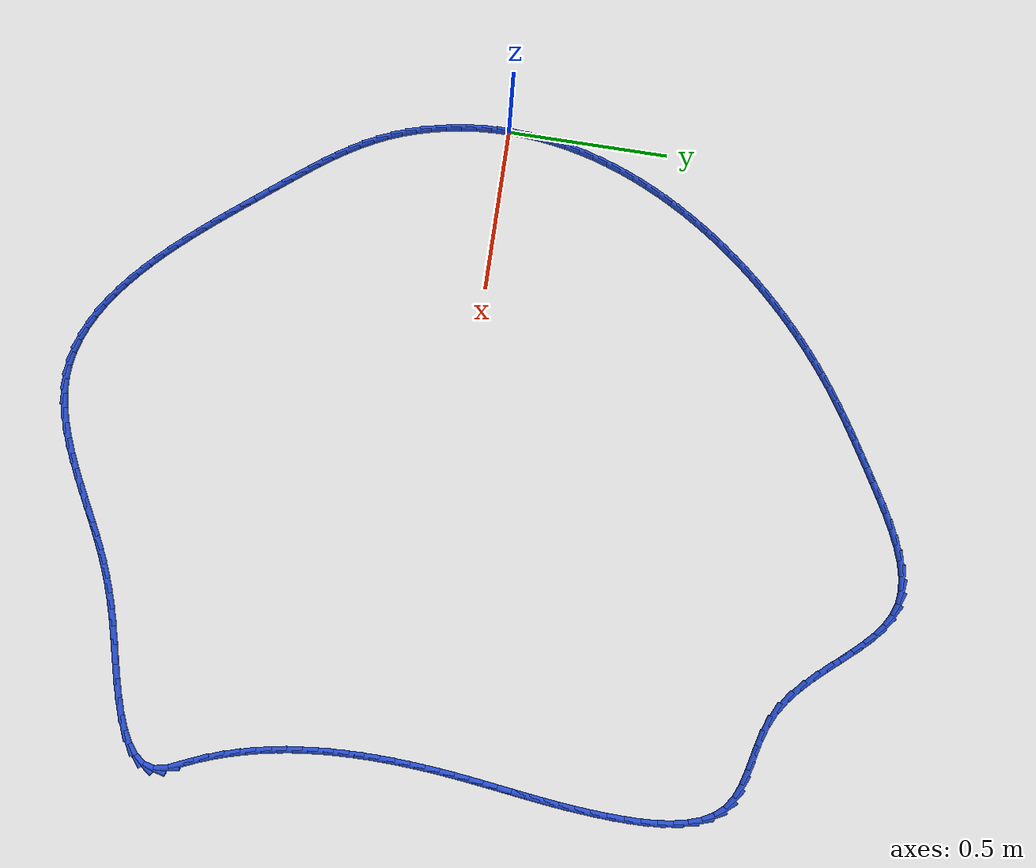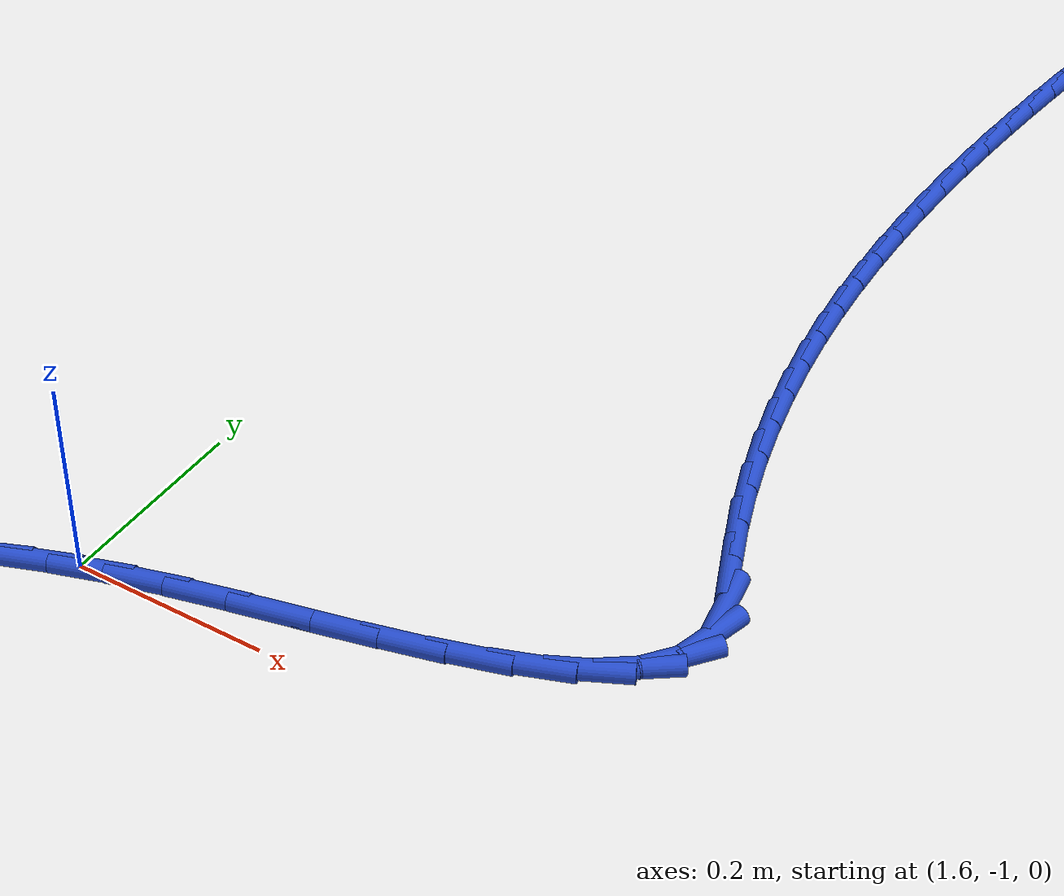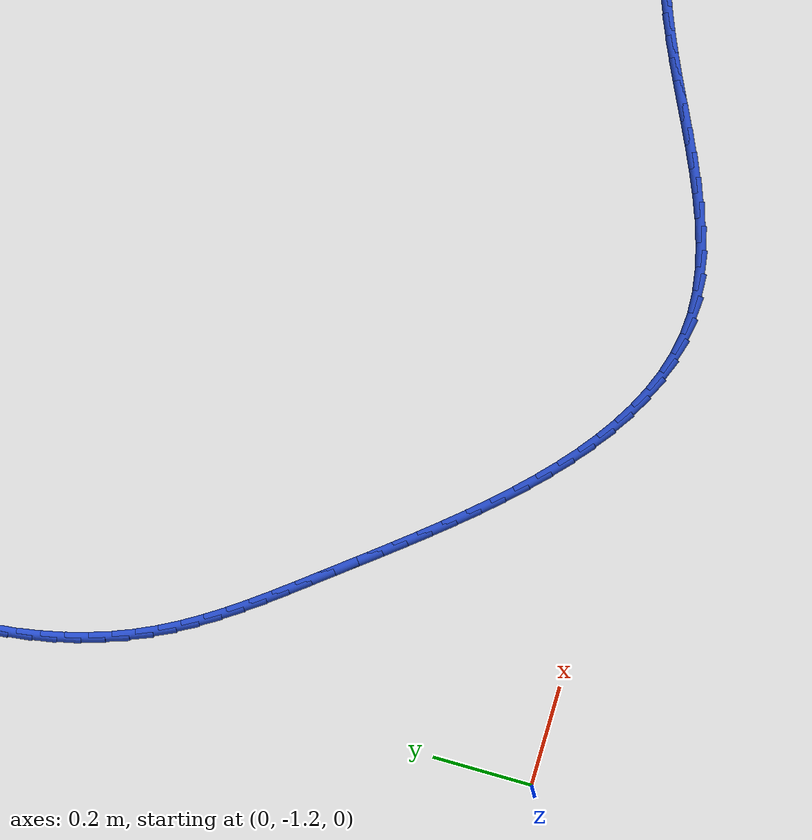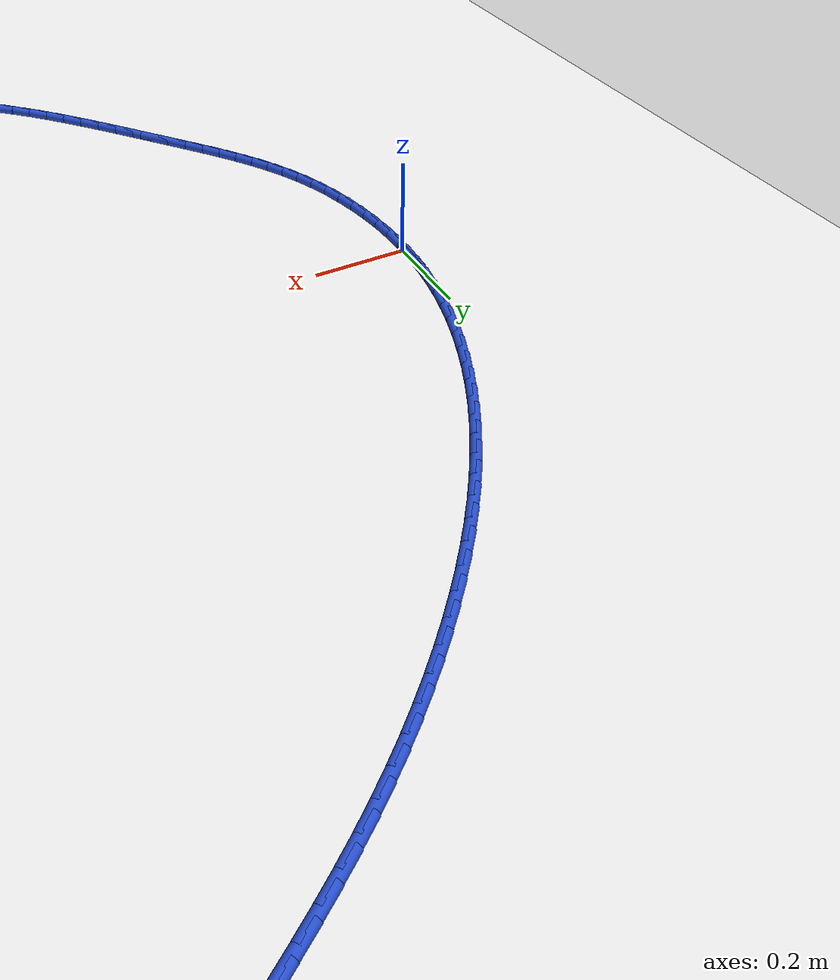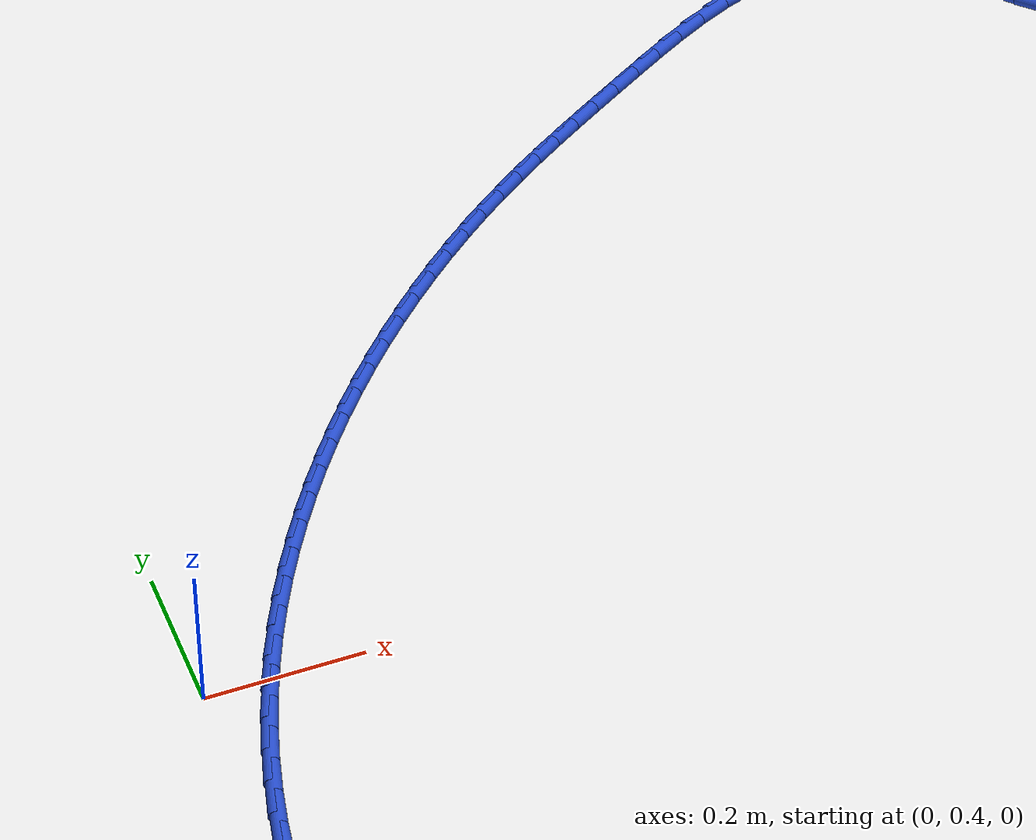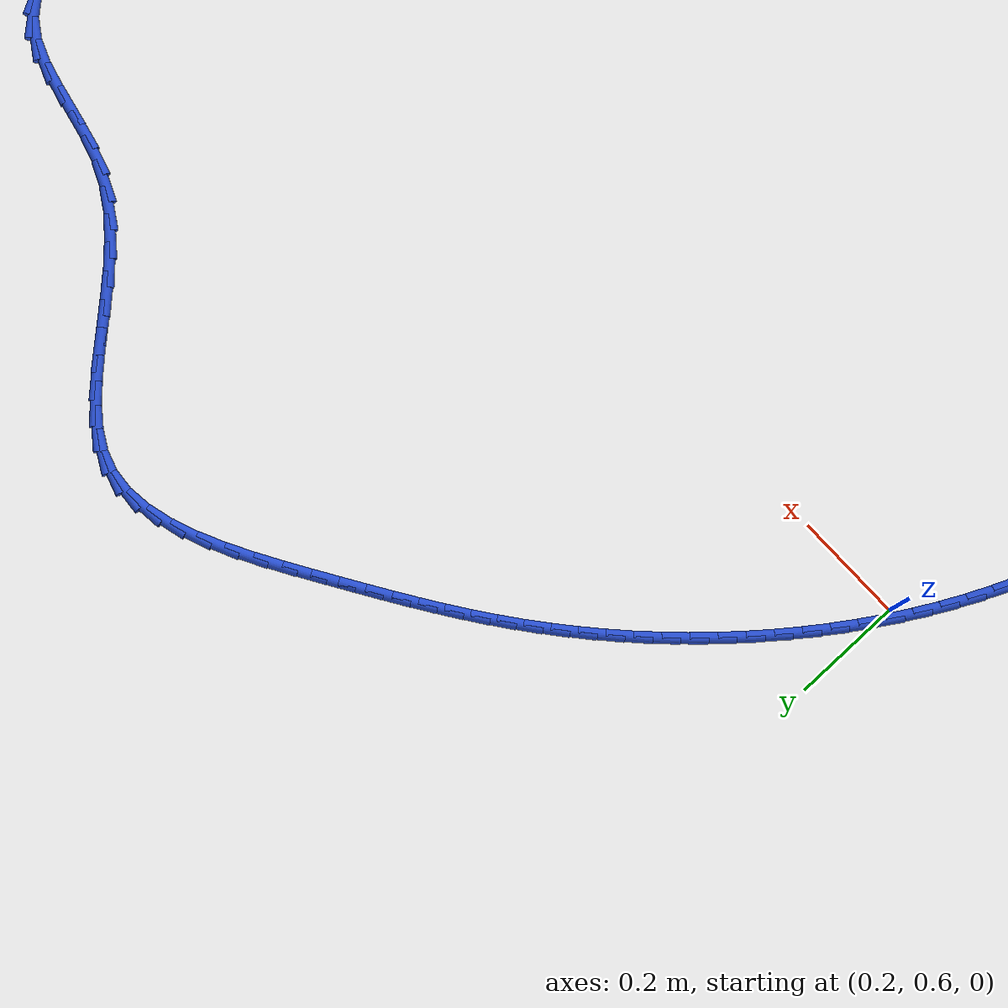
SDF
<sdf version="1.6">
 <world name="default">
  <light name="sun" type="directional">
   <pose>0 0 10 0 -0 0</pose>
   <diffuse>0.8 0.8 0.8 1</diffuse>
   <specular>0.2 0.2 0.2 1</specular>
   <attenuation>
    <range>1000</range>
    <constant>0.9</constant>
    <linear>0.01</linear>
    <quadratic>0.001</quadratic>
   </attenuation>
   <direction>-0.5 0.1 -0.9</direction>
  </light>
  <model name="ground_plane">
   <static>1</static>
   <link name="link">
    <collision name="collision">
     <geometry><plane><normal>0 0 1</normal><size>100 100</size></plane></geometry>
     <surface><friction><ode><mu>100</mu><mu2>50</mu2></ode></friction></surface>
    </collision>
    <visual name="visual">
     <cast_shadows>0</cast_shadows>
     <geometry><plane><normal>0 0 1</normal><size>100 100</size></plane></geometry>
     <material>
      <script><uri>file://media/materials/scripts/gazebo.material</uri><name>Gazebo/WhiteGlow</name></script>
     </material>
    </visual>
   </link>
  </model>
  <gravity>0 0 -9.8</gravity>
  <magnetic_field>6e-06 2.3e-05 -4.2e-05</magnetic_field>
  <atmosphere type="adiabatic"/>
  <physics name="default_physics" default="0" type="ode">
   <max_step_size>0.001</max_step_size>
   <real_time_factor>1</real_time_factor>
   <real_time_update_rate>1000</real_time_update_rate>
  </physics>
  <scene><ambient>0.4 0.4 0.4 1</ambient><background>0.7 0.7 0.7 1</background><shadows>1</shadows></scene>
  <spherical_coordinates>
   <surface_model>EARTH_WGS84</surface_model>
   <latitude_deg>0</latitude_deg>
   <longitude_deg>0</longitude_deg>
   <elevation>0</elevation>
   <heading_deg>0</heading_deg>
  </spherical_coordinates>
  <model name="line">
   <link name="link_0">
    <pose>1.214306433183765e-17 -4.163336342344337e-17 0.01 0 1.57 1.5372497949093846</pose>
    <collision name="collision">
     <geometry><cylinder><radius>0.01</radius><length>0.08</length></cylinder></geometry>
    </collision>
    <visual name="visual">
     <material>
      <script><name>Gazebo/Blue</name><uri>file://media/materials/scripts/gazebo.material</uri></script>
     </material>
     <geometry><cylinder><radius>0.01</radius><length>0.08</length></cylinder></geometry>
    </visual>
   </link>
   <link name="link_1">
    <pose>0.0015873954386153588 0.047301459667661416 0.01 0 1.57 1.489936352947675</pose>
    <collision name="collision">
     <geometry><cylinder><radius>0.01</radius><length>0.08</length></cylinder></geometry>
    </collision>
    <visual name="visual">
     <material>
      <script><name>Gazebo/Blue</name><uri>file://media/materials/scripts/gazebo.material</uri></script>
     </material>
     <geometry><cylinder><radius>0.01</radius><length>0.08</length></cylinder></geometry>
    </visual>
   </link>
   <link name="link_2">
    <pose>0.005396834196003874 0.09431028854311867 0.01 0 1.57 1.4438797213239627</pose>
    <collision name="collision">
     <geometry><cylinder><radius>0.01</radius><length>0.08</length></cylinder></geometry>
    </collision>
    <visual name="visual">
     <material>
      <script><name>Gazebo/Blue</name><uri>file://media/materials/scripts/gazebo.material</uri></script>
     </material>
     <geometry><cylinder><radius>0.01</radius><length>0.08</length></cylinder></geometry>
    </visual>
   </link>
   <link name="link_3">
    <pose>0.01135394481383041 0.14099520286789244 0.01 0 1.57 1.3991697899921811</pose>
    <collision name="collision">
     <geometry><cylinder><radius>0.01</radius><length>0.08</length></cylinder></geometry>
    </collision>
    <visual name="visual">
     <material>
      <script><name>Gazebo/Blue</name><uri>file://media/materials/scripts/gazebo.material</uri></script>
     </material>
     <geometry><cylinder><radius>0.01</radius><length>0.08</length></cylinder></geometry>
    </visual>
   </link>
   <link name="link_4">
    <pose>0.019384355833759824 0.18732491888350322 0.01 0 1.57 1.3558695304690316</pose>
    <collision name="collision">
     <geometry><cylinder><radius>0.01</radius><length>0.08</length></cylinder></geometry>
    </collision>
    <visual name="visual">
     <material>
      <script><name>Gazebo/Blue</name><uri>file://media/materials/scripts/gazebo.material</uri></script>
     </material>
     <geometry><cylinder><radius>0.01</radius><length>0.08</length></cylinder></geometry>
    </visual>
   </link>
   <link name="link_5">
    <pose>0.029413695797456972 0.23326815283147184 0.01 0 1.57 1.314016853170868</pose>
    <collision name="collision">
     <geometry><cylinder><radius>0.01</radius><length>0.08</length></cylinder></geometry>
    </collision>
    <visual name="visual">
     <material>
      <script><name>Gazebo/Blue</name><uri>file://media/materials/scripts/gazebo.material</uri></script>
     </material>
     <geometry><cylinder><radius>0.01</radius><length>0.08</length></cylinder></geometry>
    </visual>
   </link>
   <link name="link_6">
    <pose>0.04136759324658672 0.2787936209533189 0.01 0 1.57 1.2736270512572747</pose>
    <collision name="collision">
     <geometry><cylinder><radius>0.01</radius><length>0.08</length></cylinder></geometry>
    </collision>
    <visual name="visual">
     <material>
      <script><name>Gazebo/Blue</name><uri>file://media/materials/scripts/gazebo.material</uri></script>
     </material>
     <geometry><cylinder><radius>0.01</radius><length>0.08</length></cylinder></geometry>
    </visual>
   </link>
   <link name="link_7">
    <pose>0.055171676722813895 0.3238700394905648 0.01 0 1.57 1.234695579645177</pose>
    <collision name="collision">
     <geometry><cylinder><radius>0.01</radius><length>0.08</length></cylinder></geometry>
    </collision>
    <visual name="visual">
     <material>
      <script><name>Gazebo/Blue</name><uri>file://media/materials/scripts/gazebo.material</uri></script>
     </material>
     <geometry><cylinder><radius>0.01</radius><length>0.08</length></cylinder></geometry>
    </visual>
   </link>
   <link name="link_8">
    <pose>0.07075157476780337 0.36846612468473056 0.01 0 1.57 1.1971938949251435</pose>
    <collision name="collision">
     <geometry><cylinder><radius>0.01</radius><length>0.08</length></cylinder></geometry>
    </collision>
    <visual name="visual">
     <material>
      <script><name>Gazebo/Blue</name><uri>file://media/materials/scripts/gazebo.material</uri></script>
     </material>
     <geometry><cylinder><radius>0.01</radius><length>0.08</length></cylinder></geometry>
    </visual>
   </link>
   <link name="link_9">
    <pose>0.08803316975666235 0.41255032458278174 0.01 0 1.57 1.1610065011993582</pose>
    <collision name="collision">
     <geometry><cylinder><radius>0.01</radius><length>0.08</length></cylinder></geometry>
    </collision>
    <visual name="visual">
     <material>
      <script><name>Gazebo/Blue</name><uri>file://media/materials/scripts/gazebo.material</uri></script>
     </material>
     <geometry><cylinder><radius>0.01</radius><length>0.08</length></cylinder></geometry>
    </visual>
   </link>
   <link name="link_10">
    <pose>0.10694516865642821 0.45608810283306345 0.01 0 1.57 1.1260330669258578</pose>
    <collision name="collision">
     <geometry><cylinder><radius>0.01</radius><length>0.08</length></cylinder></geometry>
    </collision>
    <visual name="visual">
     <material>
      <script><name>Gazebo/Blue</name><uri>file://media/materials/scripts/gazebo.material</uri></script>
     </material>
     <geometry><cylinder><radius>0.01</radius><length>0.08</length></cylinder></geometry>
    </visual>
   </link>
   <link name="link_11">
    <pose>0.12741804255354874 0.49904305915608 0.01 0 1.57 1.092213098332053</pose>
    <collision name="collision">
     <geometry><cylinder><radius>0.01</radius><length>0.08</length></cylinder></geometry>
    </collision>
    <visual name="visual">
     <material>
      <script><name>Gazebo/Blue</name><uri>file://media/materials/scripts/gazebo.material</uri></script>
     </material>
     <geometry><cylinder><radius>0.01</radius><length>0.08</length></cylinder></geometry>
    </visual>
   </link>
   <link name="link_12">
    <pose>0.14938228942897605 0.5413787648562244 0.01 0 1.57 1.0594809484683612</pose>
    <collision name="collision">
     <geometry><cylinder><radius>0.01</radius><length>0.08</length></cylinder></geometry>
    </collision>
    <visual name="visual">
     <material>
      <script><name>Gazebo/Blue</name><uri>file://media/materials/scripts/gazebo.material</uri></script>
     </material>
     <geometry><cylinder><radius>0.01</radius><length>0.08</length></cylinder></geometry>
    </visual>
   </link>
   <link name="link_13">
    <pose>0.172768407263662 0.5830587912378887 0.01 0 1.57 1.0277665312381554</pose>
    <collision name="collision">
     <geometry><cylinder><radius>0.01</radius><length>0.08</length></cylinder></geometry>
    </collision>
    <visual name="visual">
     <material>
      <script><name>Gazebo/Blue</name><uri>file://media/materials/scripts/gazebo.material</uri></script>
     </material>
     <geometry><cylinder><radius>0.01</radius><length>0.08</length></cylinder></geometry>
    </visual>
   </link>
   <link name="link_14">
    <pose>0.1975068940385587 0.6240467096054656 0.01 0 1.57 0.9969965068718447</pose>
    <collision name="collision">
     <geometry><cylinder><radius>0.01</radius><length>0.08</length></cylinder></geometry>
    </collision>
    <visual name="visual">
     <material>
      <script><name>Gazebo/Blue</name><uri>file://media/materials/scripts/gazebo.material</uri></script>
     </material>
     <geometry><cylinder><radius>0.01</radius><length>0.08</length></cylinder></geometry>
    </visual>
   </link>
   <link name="link_15">
    <pose>0.22352824773461824 0.6643060912633478 0.01 0 1.57 0.9670952088650392</pose>
    <collision name="collision">
     <geometry><cylinder><radius>0.01</radius><length>0.08</length></cylinder></geometry>
    </collision>
    <visual name="visual">
     <material>
      <script><name>Gazebo/Blue</name><uri>file://media/materials/scripts/gazebo.material</uri></script>
     </material>
     <geometry><cylinder><radius>0.01</radius><length>0.08</length></cylinder></geometry>
    </visual>
   </link>
   <link name="link_16">
    <pose>0.2507629663327925 0.7038005075159275 0.01 0 1.57 0.9379853351118747</pose>
    <collision name="collision">
     <geometry><cylinder><radius>0.01</radius><length>0.08</length></cylinder></geometry>
    </collision>
    <visual name="visual">
     <material>
      <script><name>Gazebo/Blue</name><uri>file://media/materials/scripts/gazebo.material</uri></script>
     </material>
     <geometry><cylinder><radius>0.01</radius><length>0.08</length></cylinder></geometry>
    </visual>
   </link>
   <link name="link_17">
    <pose>0.27914154781403366 0.7424935296675973 0.01 0 1.57 0.909588427660407</pose>
    <collision name="collision">
     <geometry><cylinder><radius>0.01</radius><length>0.08</length></cylinder></geometry>
    </collision>
    <visual name="visual">
     <material>
      <script><name>Gazebo/Blue</name><uri>file://media/materials/scripts/gazebo.material</uri></script>
     </material>
     <geometry><cylinder><radius>0.01</radius><length>0.08</length></cylinder></geometry>
    </visual>
   </link>
   <link name="link_18">
    <pose>0.3085944901592935 0.7803487290227495 0.01 0 1.57 0.881825164968382</pose>
    <collision name="collision">
     <geometry><cylinder><radius>0.01</radius><length>0.08</length></cylinder></geometry>
    </collision>
    <visual name="visual">
     <material>
      <script><name>Gazebo/Blue</name><uri>file://media/materials/scripts/gazebo.material</uri></script>
     </material>
     <geometry><cylinder><radius>0.01</radius><length>0.08</length></cylinder></geometry>
    </visual>
   </link>
   <link name="link_19">
    <pose>0.3390522913495243 0.8173296768857771 0.01 0 1.57 0.8546154885025559</pose>
    <collision name="collision">
     <geometry><cylinder><radius>0.01</radius><length>0.08</length></cylinder></geometry>
    </collision>
    <visual name="visual">
     <material>
      <script><name>Gazebo/Blue</name><uri>file://media/materials/scripts/gazebo.material</uri></script>
     </material>
     <geometry><cylinder><radius>0.01</radius><length>0.08</length></cylinder></geometry>
    </visual>
   </link>
   <link name="link_20">
    <pose>0.37044544936567797 0.8533999445610723 0.01 0 1.57 0.8278785825809821</pose>
    <collision name="collision">
     <geometry><cylinder><radius>0.01</radius><length>0.08</length></cylinder></geometry>
    </collision>
    <visual name="visual">
     <material>
      <script><name>Gazebo/Blue</name><uri>file://media/materials/scripts/gazebo.material</uri></script>
     </material>
     <geometry><cylinder><radius>0.01</radius><length>0.08</length></cylinder></geometry>
    </visual>
   </link>
   <link name="link_21">
    <pose>0.40270446218870654 0.8885231033530276 0.01 0 1.57 0.8015327229210458</pose>
    <collision name="collision">
     <geometry><cylinder><radius>0.01</radius><length>0.08</length></cylinder></geometry>
    </collision>
    <visual name="visual">
     <material>
      <script><name>Gazebo/Blue</name><uri>file://media/materials/scripts/gazebo.material</uri></script>
     </material>
     <geometry><cylinder><radius>0.01</radius><length>0.08</length></cylinder></geometry>
    </visual>
   </link>
   <link name="link_22">
    <pose>0.43575982779956207 0.9226627245660355 0.01 0 1.57 0.775495005708522</pose>
    <collision name="collision">
     <geometry><cylinder><radius>0.01</radius><length>0.08</length></cylinder></geometry>
    </collision>
    <visual name="visual">
     <material>
      <script><name>Gazebo/Blue</name><uri>file://media/materials/scripts/gazebo.material</uri></script>
     </material>
     <geometry><cylinder><radius>0.01</radius><length>0.08</length></cylinder></geometry>
    </visual>
   </link>
   <link name="link_23">
    <pose>0.46954204417919654 0.9557823795044883 0.01 0 1.57 0.7496809653231622</pose>
    <collision name="collision">
     <geometry><cylinder><radius>0.01</radius><length>0.08</length></cylinder></geometry>
    </collision>
    <visual name="visual">
     <material>
      <script><name>Gazebo/Blue</name><uri>file://media/materials/scripts/gazebo.material</uri></script>
     </material>
     <geometry><cylinder><radius>0.01</radius><length>0.08</length></cylinder></geometry>
    </visual>
   </link>
   <link name="link_24">
    <pose>0.5039816093085618 0.9878456394727786 0.01 0 1.57 0.7240040852488039</pose>
    <collision name="collision">
     <geometry><cylinder><radius>0.01</radius><length>0.08</length></cylinder></geometry>
    </collision>
    <visual name="visual">
     <material>
      <script><name>Gazebo/Blue</name><uri>file://media/materials/scripts/gazebo.material</uri></script>
     </material>
     <geometry><cylinder><radius>0.01</radius><length>0.08</length></cylinder></geometry>
    </visual>
   </link>
   <link name="link_25">
    <pose>0.5390090211686103 1.0188160757752995 0.01 0 1.57 0.6983752032161585</pose>
    <collision name="collision">
     <geometry><cylinder><radius>0.01</radius><length>0.08</length></cylinder></geometry>
    </collision>
    <visual name="visual">
     <material>
      <script><name>Gazebo/Blue</name><uri>file://media/materials/scripts/gazebo.material</uri></script>
     </material>
     <geometry><cylinder><radius>0.01</radius><length>0.08</length></cylinder></geometry>
    </visual>
   </link>
   <link name="link_26">
    <pose>0.5745547777402935 1.0486572597164425 0.01 0 1.57 0.6727018083050694</pose>
    <collision name="collision">
     <geometry><cylinder><radius>0.01</radius><length>0.08</length></cylinder></geometry>
    </collision>
    <visual name="visual">
     <material>
      <script><name>Gazebo/Blue</name><uri>file://media/materials/scripts/gazebo.material</uri></script>
     </material>
     <geometry><cylinder><radius>0.01</radius><length>0.08</length></cylinder></geometry>
    </visual>
   </link>
   <link name="link_27">
    <pose>0.6105493770045638 1.0773327626006008 0.01 0 1.57 0.6470819854404947</pose>
    <collision name="collision">
     <geometry><cylinder><radius>0.01</radius><length>0.08</length></cylinder></geometry>
    </collision>
    <visual name="visual">
     <material>
      <script><name>Gazebo/Blue</name><uri>file://media/materials/scripts/gazebo.material</uri></script>
     </material>
     <geometry><cylinder><radius>0.01</radius><length>0.08</length></cylinder></geometry>
    </visual>
   </link>
   <link name="link_28">
    <pose>0.6469410172642722 1.1048306575702471 0.01 0 1.57 0.6231741964512322</pose>
    <collision name="collision">
     <geometry><cylinder><radius>0.01</radius><length>0.08</length></cylinder></geometry>
    </collision>
    <visual name="visual">
     <material>
      <script><name>Gazebo/Blue</name><uri>file://media/materials/scripts/gazebo.material</uri></script>
     </material>
     <geometry><cylinder><radius>0.01</radius><length>0.08</length></cylinder></geometry>
    </visual>
   </link>
   <link name="link_29">
    <pose>0.6838204436448937 1.1313363395559395 0.01 0 1.57 0.602186844409367</pose>
    <collision name="collision">
     <geometry><cylinder><radius>0.01</radius><length>0.08</length></cylinder></geometry>
    </collision>
    <visual name="visual">
     <material>
      <script><name>Gazebo/Blue</name><uri>file://media/materials/scripts/gazebo.material</uri></script>
     </material>
     <geometry><cylinder><radius>0.01</radius><length>0.08</length></cylinder></geometry>
    </visual>
   </link>
   <link name="link_30">
    <pose>0.7213471885588422 1.1571304229410908 0.01 0 1.57 0.5845214186268726</pose>
    <collision name="collision">
     <geometry><cylinder><radius>0.01</radius><length>0.08</length></cylinder></geometry>
    </collision>
    <visual name="visual">
     <material>
      <script><name>Gazebo/Blue</name><uri>file://media/materials/scripts/gazebo.material</uri></script>
     </material>
     <geometry><cylinder><radius>0.01</radius><length>0.08</length></cylinder></geometry>
    </visual>
   </link>
   <link name="link_31">
    <pose>0.7596812288100578 1.1824941372622877 0.01 0 1.57 0.5704267616512975</pose>
    <collision name="collision">
     <geometry><cylinder><radius>0.01</radius><length>0.08</length></cylinder></geometry>
    </collision>
    <visual name="visual">
     <material>
      <script><name>Gazebo/Blue</name><uri>file://media/materials/scripts/gazebo.material</uri></script>
     </material>
     <geometry><cylinder><radius>0.01</radius><length>0.08</length></cylinder></geometry>
    </visual>
   </link>
   <link name="link_32">
    <pose>0.7989825412024805 1.2077087120561174 0.01 0 1.57 0.5599999479686203</pose>
    <collision name="collision">
     <geometry><cylinder><radius>0.01</radius><length>0.08</length></cylinder></geometry>
    </collision>
    <visual name="visual">
     <material>
      <script><name>Gazebo/Blue</name><uri>file://media/materials/scripts/gazebo.material</uri></script>
     </material>
     <geometry><cylinder><radius>0.01</radius><length>0.08</length></cylinder></geometry>
    </visual>
   </link>
   <link name="link_33">
    <pose>0.8394111025400496 1.2330553768591672 0.01 0 1.57 0.5531962998500586</pose>
    <collision name="collision">
     <geometry><cylinder><radius>0.01</radius><length>0.08</length></cylinder></geometry>
    </collision>
    <visual name="visual">
     <material>
      <script><name>Gazebo/Blue</name><uri>file://media/materials/scripts/gazebo.material</uri></script>
     </material>
     <geometry><cylinder><radius>0.01</radius><length>0.08</length></cylinder></geometry>
    </visual>
   </link>
   <link name="link_34">
    <pose>0.8811268896267054 1.2588153612080242 0.01 0 1.57 0.5497029477946016</pose>
    <collision name="collision">
     <geometry><cylinder><radius>0.01</radius><length>0.08</length></cylinder></geometry>
    </collision>
    <visual name="visual">
     <material>
      <script><name>Gazebo/Blue</name><uri>file://media/materials/scripts/gazebo.material</uri></script>
     </material>
     <geometry><cylinder><radius>0.01</radius><length>0.08</length></cylinder></geometry>
    </visual>
   </link>
   <link name="link_35">
    <pose>0.9242846089538607 1.285257947988467 0.01 0 1.57 0.5423663309234642</pose>
    <collision name="collision">
     <geometry><cylinder><radius>0.01</radius><length>0.08</length></cylinder></geometry>
    </collision>
    <visual name="visual">
     <material>
      <script><name>Gazebo/Blue</name><uri>file://media/materials/scripts/gazebo.material</uri></script>
     </material>
     <geometry><cylinder><radius>0.01</radius><length>0.08</length></cylinder></geometry>
    </visual>
   </link>
   <link name="link_36">
    <pose>0.9687846464274483 1.3120759307011325 0.01 0 1.57 0.5213591173747137</pose>
    <collision name="collision">
     <geometry><cylinder><radius>0.01</radius><length>0.08</length></cylinder></geometry>
    </collision>
    <visual name="visual">
     <material>
      <script><name>Gazebo/Blue</name><uri>file://media/materials/scripts/gazebo.material</uri></script>
     </material>
     <geometry><cylinder><radius>0.01</radius><length>0.08</length></cylinder></geometry>
    </visual>
   </link>
   <link name="link_37">
    <pose>1.0141651779996288 1.3381410517581362 0.01 0 1.57 0.48500732329421326</pose>
    <collision name="collision">
     <geometry><cylinder><radius>0.01</radius><length>0.08</length></cylinder></geometry>
    </collision>
    <visual name="visual">
     <material>
      <script><name>Gazebo/Blue</name><uri>file://media/materials/scripts/gazebo.material</uri></script>
     </material>
     <geometry><cylinder><radius>0.01</radius><length>0.08</length></cylinder></geometry>
    </visual>
   </link>
   <link name="link_38">
    <pose>1.0599366819786638 1.3622622690444524 0.01 0 1.57 0.43071782671561026</pose>
    <collision name="collision">
     <geometry><cylinder><radius>0.01</radius><length>0.08</length></cylinder></geometry>
    </collision>
    <visual name="visual">
     <material>
      <script><name>Gazebo/Blue</name><uri>file://media/materials/scripts/gazebo.material</uri></script>
     </material>
     <geometry><cylinder><radius>0.01</radius><length>0.08</length></cylinder></geometry>
    </visual>
   </link>
   <link name="link_39">
    <pose>1.1056096366728136 1.3832485404450559 0.01 0 1.57 0.35396774529181163</pose>
    <collision name="collision">
     <geometry><cylinder><radius>0.01</radius><length>0.08</length></cylinder></geometry>
    </collision>
    <visual name="visual">
     <material>
      <script><name>Gazebo/Blue</name><uri>file://media/materials/scripts/gazebo.material</uri></script>
     </material>
     <geometry><cylinder><radius>0.01</radius><length>0.08</length></cylinder></geometry>
    </visual>
   </link>
   <link name="link_40">
    <pose>1.1506945203903407 1.3999088238449218 0.01 0 1.57 0.248001118957641</pose>
    <collision name="collision">
     <geometry><cylinder><radius>0.01</radius><length>0.08</length></cylinder></geometry>
    </collision>
    <visual name="visual">
     <material>
      <script><name>Gazebo/Blue</name><uri>file://media/materials/scripts/gazebo.material</uri></script>
     </material>
     <geometry><cylinder><radius>0.01</radius><length>0.08</length></cylinder></geometry>
    </visual>
   </link>
   <link name="link_41">
    <pose>1.1947018114395063 1.4110520771290245 0.01 0 1.57 0.10412634017692955</pose>
    <collision name="collision">
     <geometry><cylinder><radius>0.01</radius><length>0.08</length></cylinder></geometry>
    </collision>
    <visual name="visual">
     <material>
      <script><name>Gazebo/Blue</name><uri>file://media/materials/scripts/gazebo.material</uri></script>
     </material>
     <geometry><cylinder><radius>0.01</radius><length>0.08</length></cylinder></geometry>
    </visual>
   </link>
   <link name="link_42">
    <pose>1.2371419881285706 1.415487258182339 0.01 0 1.57 -0.08556642752042813</pose>
    <collision name="collision">
     <geometry><cylinder><radius>0.01</radius><length>0.08</length></cylinder></geometry>
    </collision>
    <visual name="visual">
     <material>
      <script><name>Gazebo/Blue</name><uri>file://media/materials/scripts/gazebo.material</uri></script>
     </material>
     <geometry><cylinder><radius>0.01</radius><length>0.08</length></cylinder></geometry>
    </visual>
   </link>
   <link name="link_43">
    <pose>1.2775255287657954 1.412023324889839 0.01 0 1.57 -0.31185970319608747</pose>
    <collision name="collision">
     <geometry><cylinder><radius>0.01</radius><length>0.08</length></cylinder></geometry>
    </collision>
    <visual name="visual">
     <material>
      <script><name>Gazebo/Blue</name><uri>file://media/materials/scripts/gazebo.material</uri></script>
     </material>
     <geometry><cylinder><radius>0.01</radius><length>0.08</length></cylinder></geometry>
    </visual>
   </link>
   <link name="link_44">
    <pose>1.3154876858018383 1.399785112929304 0.01 0 1.57 -0.5120720492279744</pose>
    <collision name="collision">
     <geometry><cylinder><radius>0.01</radius><length>0.08</length></cylinder></geometry>
    </collision>
    <visual name="visual">
     <material>
      <script><name>Gazebo/Blue</name><uri>file://media/materials/scripts/gazebo.material</uri></script>
     </material>
     <geometry><cylinder><radius>0.01</radius><length>0.08</length></cylinder></geometry>
    </visual>
   </link>
   <link name="link_45">
    <pose>1.351347633939852 1.3796288732174433 0.01 0 1.57 -0.6599936482553092</pose>
    <collision name="collision">
     <geometry><cylinder><radius>0.01</radius><length>0.08</length></cylinder></geometry>
    </collision>
    <visual name="visual">
     <material>
      <script><name>Gazebo/Blue</name><uri>file://media/materials/scripts/gazebo.material</uri></script>
     </material>
     <geometry><cylinder><radius>0.01</radius><length>0.08</length></cylinder></geometry>
    </visual>
   </link>
   <link name="link_46">
    <pose>1.3856576721279887 1.3530010332135192 0.01 0 1.57 -0.7598498416399019</pose>
    <collision name="collision">
     <geometry><cylinder><radius>0.01</radius><length>0.08</length></cylinder></geometry>
    </collision>
    <visual name="visual">
     <material>
      <script><name>Gazebo/Blue</name><uri>file://media/materials/scripts/gazebo.material</uri></script>
     </material>
     <geometry><cylinder><radius>0.01</radius><length>0.08</length></cylinder></geometry>
    </visual>
   </link>
   <link name="link_47">
    <pose>1.4189702967042257 1.3213485200882036 0.01 0 1.57 -0.82007768028849</pose>
    <collision name="collision">
     <geometry><cylinder><radius>0.01</radius><length>0.08</length></cylinder></geometry>
    </collision>
    <visual name="visual">
     <material>
      <script><name>Gazebo/Blue</name><uri>file://media/materials/scripts/gazebo.material</uri></script>
     </material>
     <geometry><cylinder><radius>0.01</radius><length>0.08</length></cylinder></geometry>
    </visual>
   </link>
   <link name="link_48">
    <pose>1.451838004006542 1.2861182610121689 0.01 0 1.57 -0.8476720759975318</pose>
    <collision name="collision">
     <geometry><cylinder><radius>0.01</radius><length>0.08</length></cylinder></geometry>
    </collision>
    <visual name="visual">
     <material>
      <script><name>Gazebo/Blue</name><uri>file://media/materials/scripts/gazebo.material</uri></script>
     </material>
     <geometry><cylinder><radius>0.01</radius><length>0.08</length></cylinder></geometry>
    </visual>
   </link>
   <link name="link_49">
    <pose>1.4848132903729134 1.248757183156087 0.01 0 1.57 -0.8468384163667483</pose>
    <collision name="collision">
     <geometry><cylinder><radius>0.01</radius><length>0.08</length></cylinder></geometry>
    </collision>
    <visual name="visual">
     <material>
      <script><name>Gazebo/Blue</name><uri>file://media/materials/scripts/gazebo.material</uri></script>
     </material>
     <geometry><cylinder><radius>0.01</radius><length>0.08</length></cylinder></geometry>
    </visual>
   </link>
   <link name="link_50">
    <pose>1.518448652141319 1.2107122136906296 0.01 0 1.57 -0.8191300590002366</pose>
    <collision name="collision">
     <geometry><cylinder><radius>0.01</radius><length>0.08</length></cylinder></geometry>
    </collision>
    <visual name="visual">
     <material>
      <script><name>Gazebo/Blue</name><uri>file://media/materials/scripts/gazebo.material</uri></script>
     </material>
     <geometry><cylinder><radius>0.01</radius><length>0.08</length></cylinder></geometry>
    </visual>
   </link>
   <link name="link_51">
    <pose>1.5532965856497365 1.1734302797864689 0.01 0 1.57 -0.7639042151658584</pose>
    <collision name="collision">
     <geometry><cylinder><radius>0.01</radius><length>0.08</length></cylinder></geometry>
    </collision>
    <visual name="visual">
     <material>
      <script><name>Gazebo/Blue</name><uri>file://media/materials/scripts/gazebo.material</uri></script>
     </material>
     <geometry><cylinder><radius>0.01</radius><length>0.08</length></cylinder></geometry>
    </visual>
   </link>
   <link name="link_52">
    <pose>1.5899095872361433 1.1383583086142774 0.01 0 1.57 -0.6789653528277156</pose>
    <collision name="collision">
     <geometry><cylinder><radius>0.01</radius><length>0.08</length></cylinder></geometry>
    </collision>
    <visual name="visual">
     <material>
      <script><name>Gazebo/Blue</name><uri>file://media/materials/scripts/gazebo.material</uri></script>
     </material>
     <geometry><cylinder><radius>0.01</radius><length>0.08</length></cylinder></geometry>
    </visual>
   </link>
   <link name="link_53">
    <pose>1.6288401532385177 1.1069432273447264 0.01 0 1.57 -0.5617905130435357</pose>
    <collision name="collision">
     <geometry><cylinder><radius>0.01</radius><length>0.08</length></cylinder></geometry>
    </collision>
    <visual name="visual">
     <material>
      <script><name>Gazebo/Blue</name><uri>file://media/materials/scripts/gazebo.material</uri></script>
     </material>
     <geometry><cylinder><radius>0.01</radius><length>0.08</length></cylinder></geometry>
    </visual>
   </link>
   <link name="link_54">
    <pose>1.6706407799948368 1.0806319631484886 0.01 0 1.57 -0.41496245748131144</pose>
    <collision name="collision">
     <geometry><cylinder><radius>0.01</radius><length>0.08</length></cylinder></geometry>
    </collision>
    <visual name="visual">
     <material>
      <script><name>Gazebo/Blue</name><uri>file://media/materials/scripts/gazebo.material</uri></script>
     </material>
     <geometry><cylinder><radius>0.01</radius><length>0.08</length></cylinder></geometry>
    </visual>
   </link>
   <link name="link_55">
    <pose>1.7157879506794882 1.0607426528257258 0.01 0 1.57 -0.2897167532969112</pose>
    <collision name="collision">
     <geometry><cylinder><radius>0.01</radius><length>0.08</length></cylinder></geometry>
    </collision>
    <visual name="visual">
     <material>
      <script><name>Gazebo/Blue</name><uri>file://media/materials/scripts/gazebo.material</uri></script>
     </material>
     <geometry><cylinder><radius>0.01</radius><length>0.08</length></cylinder></geometry>
    </visual>
   </link>
   <link name="link_56">
    <pose>1.7635289860777958 1.046510842845819 0.01 0 1.57 -0.2231429391512614</pose>
    <collision name="collision">
     <geometry><cylinder><radius>0.01</radius><length>0.08</length></cylinder></geometry>
    </collision>
    <visual name="visual">
     <material>
      <script><name>Gazebo/Blue</name><uri>file://media/materials/scripts/gazebo.material</uri></script>
     </material>
     <geometry><cylinder><radius>0.01</radius><length>0.08</length></cylinder></geometry>
    </visual>
   </link>
   <link name="link_57">
    <pose>1.8121157415735316 1.0354854460499685 0.01 0 1.57 -0.2132315533554481</pose>
    <collision name="collision">
     <geometry><cylinder><radius>0.01</radius><length>0.08</length></cylinder></geometry>
    </collision>
    <visual name="visual">
     <material>
      <script><name>Gazebo/Blue</name><uri>file://media/materials/scripts/gazebo.material</uri></script>
     </material>
     <geometry><cylinder><radius>0.01</radius><length>0.08</length></cylinder></geometry>
    </visual>
   </link>
   <link name="link_58">
    <pose>1.859771451305368 1.0251668818265693 0.01 0 1.57 -0.26320123160877457</pose>
    <collision name="collision">
     <geometry><cylinder><radius>0.01</radius><length>0.08</length></cylinder></geometry>
    </collision>
    <visual name="visual">
     <material>
      <script><name>Gazebo/Blue</name><uri>file://media/materials/scripts/gazebo.material</uri></script>
     </material>
     <geometry><cylinder><radius>0.01</radius><length>0.08</length></cylinder></geometry>
    </visual>
   </link>
   <link name="link_59">
    <pose>1.9047193494119778 1.0130555695640182 0.01 0 1.57 -0.38514884669716004</pose>
    <collision name="collision">
     <geometry><cylinder><radius>0.01</radius><length>0.08</length></cylinder></geometry>
    </collision>
    <visual name="visual">
     <material>
      <script><name>Gazebo/Blue</name><uri>file://media/materials/scripts/gazebo.material</uri></script>
     </material>
     <geometry><cylinder><radius>0.01</radius><length>0.08</length></cylinder></geometry>
    </visual>
   </link>
   <link name="link_60">
    <pose>1.9451826700320336 0.996651928650711 0.01 0 1.57 -0.5956292241043596</pose>
    <collision name="collision">
     <geometry><cylinder><radius>0.01</radius><length>0.08</length></cylinder></geometry>
    </collision>
    <visual name="visual">
     <material>
      <script><name>Gazebo/Blue</name><uri>file://media/materials/scripts/gazebo.material</uri></script>
     </material>
     <geometry><cylinder><radius>0.01</radius><length>0.08</length></cylinder></geometry>
    </visual>
   </link>
   <link name="link_61">
    <pose>1.979391846290921 0.9734670217352731 0.01 0 1.57 -0.8578289998630426</pose>
    <collision name="collision">
     <geometry><cylinder><radius>0.01</radius><length>0.08</length></cylinder></geometry>
    </collision>
    <visual name="visual">
     <material>
      <script><name>Gazebo/Blue</name><uri>file://media/materials/scripts/gazebo.material</uri></script>
     </material>
     <geometry><cylinder><radius>0.01</radius><length>0.08</length></cylinder></geometry>
    </visual>
   </link>
   <link name="link_62">
    <pose>2.0064017972001515 0.9422308632703268 0.01 0 1.57 -1.0797163538975796</pose>
    <collision name="collision">
     <geometry><cylinder><radius>0.01</radius><length>0.08</length></cylinder></geometry>
    </collision>
    <visual name="visual">
     <material>
      <script><name>Gazebo/Blue</name><uri>file://media/materials/scripts/gazebo.material</uri></script>
     </material>
     <geometry><cylinder><radius>0.01</radius><length>0.08</length></cylinder></geometry>
    </visual>
   </link>
   <link name="link_63">
    <pose>2.026844249015705 0.9040046804891455 0.01 0 1.57 -1.2479436493516618</pose>
    <collision name="collision">
     <geometry><cylinder><radius>0.01</radius><length>0.08</length></cylinder></geometry>
    </collision>
    <visual name="visual">
     <material>
      <script><name>Gazebo/Blue</name><uri>file://media/materials/scripts/gazebo.material</uri></script>
     </material>
     <geometry><cylinder><radius>0.01</radius><length>0.08</length></cylinder></geometry>
    </visual>
   </link>
   <link name="link_64">
    <pose>2.041528724476406 0.8601125618178415 0.01 0 1.57 -1.3716226393590898</pose>
    <collision name="collision">
     <geometry><cylinder><radius>0.01</radius><length>0.08</length></cylinder></geometry>
    </collision>
    <visual name="visual">
     <material>
      <script><name>Gazebo/Blue</name><uri>file://media/materials/scripts/gazebo.material</uri></script>
     </material>
     <geometry><cylinder><radius>0.01</radius><length>0.08</length></cylinder></geometry>
    </visual>
   </link>
   <link name="link_65">
    <pose>2.0512647463210762 0.8118785956825244 0.01 0 1.57 -1.4620195419599558</pose>
    <collision name="collision">
     <geometry><cylinder><radius>0.01</radius><length>0.08</length></cylinder></geometry>
    </collision>
    <visual name="visual">
     <material>
      <script><name>Gazebo/Blue</name><uri>file://media/materials/scripts/gazebo.material</uri></script>
     </material>
     <geometry><cylinder><radius>0.01</radius><length>0.08</length></cylinder></geometry>
    </visual>
   </link>
   <link name="link_66">
    <pose>2.0568618372885377 0.7606268705093041 0.01 0 1.57 -1.5279918928683596</pose>
    <collision name="collision">
     <geometry><cylinder><radius>0.01</radius><length>0.08</length></cylinder></geometry>
    </collision>
    <visual name="visual">
     <material>
      <script><name>Gazebo/Blue</name><uri>file://media/materials/scripts/gazebo.material</uri></script>
     </material>
     <geometry><cylinder><radius>0.01</radius><length>0.08</length></cylinder></geometry>
    </visual>
   </link>
   <link name="link_67">
    <pose>2.059129520117613 0.7076814747242919 0.01 0 1.57 1.5660659358439957</pose>
    <collision name="collision">
     <geometry><cylinder><radius>0.01</radius><length>0.08</length></cylinder></geometry>
    </collision>
    <visual name="visual">
     <material>
      <script><name>Gazebo/Blue</name><uri>file://media/materials/scripts/gazebo.material</uri></script>
     </material>
     <geometry><cylinder><radius>0.01</radius><length>0.08</length></cylinder></geometry>
    </visual>
   </link>
   <link name="link_68">
    <pose>2.058877317547125 0.6543664967535976 0.01 0 1.57 1.5333139351230123</pose>
    <collision name="collision">
     <geometry><cylinder><radius>0.01</radius><length>0.08</length></cylinder></geometry>
    </collision>
    <visual name="visual">
     <material>
      <script><name>Gazebo/Blue</name><uri>file://media/materials/scripts/gazebo.material</uri></script>
     </material>
     <geometry><cylinder><radius>0.01</radius><length>0.08</length></cylinder></geometry>
    </visual>
   </link>
   <link name="link_69">
    <pose>2.0569137056324323 0.6020034494101201 0.01 0 1.57 1.5104250547485023</pose>
    <collision name="collision">
     <geometry><cylinder><radius>0.01</radius><length>0.08</length></cylinder></geometry>
    </collision>
    <visual name="visual">
     <material>
      <script><name>Gazebo/Blue</name><uri>file://media/materials/scripts/gazebo.material</uri></script>
     </material>
     <geometry><cylinder><radius>0.01</radius><length>0.08</length></cylinder></geometry>
    </visual>
   </link>
   <link name="link_70">
    <pose>2.05385790354605 0.5514481340044691 0.01 0 1.57 1.4904682083308844</pose>
    <collision name="collision">
     <geometry><cylinder><radius>0.01</radius><length>0.08</length></cylinder></geometry>
    </collision>
    <visual name="visual">
     <material>
      <script><name>Gazebo/Blue</name><uri>file://media/materials/scripts/gazebo.material</uri></script>
     </material>
     <geometry><cylinder><radius>0.01</radius><length>0.08</length></cylinder></geometry>
    </visual>
   </link>
   <link name="link_71">
    <pose>2.049921876930879 0.5025542078288321 0.01 0 1.57 1.4730819632938281</pose>
    <collision name="collision">
     <geometry><cylinder><radius>0.01</radius><length>0.08</length></cylinder></geometry>
    </collision>
    <visual name="visual">
     <material>
      <script><name>Gazebo/Blue</name><uri>file://media/materials/scripts/gazebo.material</uri></script>
     </material>
     <geometry><cylinder><radius>0.01</radius><length>0.08</length></cylinder></geometry>
    </visual>
   </link>
   <link name="link_72">
    <pose>2.0452647400786237 0.4550452748753876 0.01 0 1.57 1.4587866242409435</pose>
    <collision name="collision">
     <geometry><cylinder><radius>0.01</radius><length>0.08</length></cylinder></geometry>
    </collision>
    <visual name="visual">
     <material>
      <script><name>Gazebo/Blue</name><uri>file://media/materials/scripts/gazebo.material</uri></script>
     </material>
     <geometry><cylinder><radius>0.01</radius><length>0.08</length></cylinder></geometry>
    </visual>
   </link>
   <link name="link_73">
    <pose>2.0400456072809874 0.4086449391363123 0.01 0 1.57 1.4480406597738205</pose>
    <collision name="collision">
     <geometry><cylinder><radius>0.01</radius><length>0.08</length></cylinder></geometry>
    </collision>
    <visual name="visual">
     <material>
      <script><name>Gazebo/Blue</name><uri>file://media/materials/scripts/gazebo.material</uri></script>
     </material>
     <geometry><cylinder><radius>0.01</radius><length>0.08</length></cylinder></geometry>
    </visual>
   </link>
   <link name="link_74">
    <pose>2.0344235928296768 0.36307680460378466 0.01 0 1.57 1.4412115677209945</pose>
    <collision name="collision">
     <geometry><cylinder><radius>0.01</radius><length>0.08</length></cylinder></geometry>
    </collision>
    <visual name="visual">
     <material>
      <script><name>Gazebo/Blue</name><uri>file://media/materials/scripts/gazebo.material</uri></script>
     </material>
     <geometry><cylinder><radius>0.01</radius><length>0.08</length></cylinder></geometry>
    </visual>
   </link>
   <link name="link_75">
    <pose>2.028557811016395 0.31806447526998194 0.01 0 1.57 1.4385513088621793</pose>
    <collision name="collision">
     <geometry><cylinder><radius>0.01</radius><length>0.08</length></cylinder></geometry>
    </collision>
    <visual name="visual">
     <material>
      <script><name>Gazebo/Blue</name><uri>file://media/materials/scripts/gazebo.material</uri></script>
     </material>
     <geometry><cylinder><radius>0.01</radius><length>0.08</length></cylinder></geometry>
    </visual>
   </link>
   <link name="link_76">
    <pose>2.022607376132846 0.27333155512708124 0.01 0 1.57 1.4401785959855262</pose>
    <collision name="collision">
     <geometry><cylinder><radius>0.01</radius><length>0.08</length></cylinder></geometry>
    </collision>
    <visual name="visual">
     <material>
      <script><name>Gazebo/Blue</name><uri>file://media/materials/scripts/gazebo.material</uri></script>
     </material>
     <geometry><cylinder><radius>0.01</radius><length>0.08</length></cylinder></geometry>
    </visual>
   </link>
   <link name="link_77">
    <pose>2.0167314024707355 0.22860164816726108 0.01 0 1.57 1.446069594749611</pose>
    <collision name="collision">
     <geometry><cylinder><radius>0.01</radius><length>0.08</length></cylinder></geometry>
    </collision>
    <visual name="visual">
     <material>
      <script><name>Gazebo/Blue</name><uri>file://media/materials/scripts/gazebo.material</uri></script>
     </material>
     <geometry><cylinder><radius>0.01</radius><length>0.08</length></cylinder></geometry>
    </visual>
   </link>
   <link name="link_78">
    <pose>2.011089001671749 0.18359837450859248 0.01 0 1.57 1.455647827383203</pose>
    <collision name="collision">
     <geometry><cylinder><radius>0.01</radius><length>0.08</length></cylinder></geometry>
    </collision>
    <visual name="visual">
     <material>
      <script><name>Gazebo/Blue</name><uri>file://media/materials/scripts/gazebo.material</uri></script>
     </material>
     <geometry><cylinder><radius>0.01</radius><length>0.08</length></cylinder></geometry>
    </visual>
   </link>
   <link name="link_79">
    <pose>2.0058281619252782 0.13811304273345065 0.01 0 1.57 1.4674138654498543</pose>
    <collision name="collision">
     <geometry><cylinder><radius>0.01</radius><length>0.08</length></cylinder></geometry>
    </collision>
    <visual name="visual">
     <material>
      <script><name>Gazebo/Blue</name><uri>file://media/materials/scripts/gazebo.material</uri></script>
     </material>
     <geometry><cylinder><radius>0.01</radius><length>0.08</length></cylinder></geometry>
    </visual>
   </link>
   <link name="link_80">
    <pose>2.001060345444525 0.09215922940085983 0.01 0 1.57 1.4810781166847422</pose>
    <collision name="collision">
     <geometry><cylinder><radius>0.01</radius><length>0.08</length></cylinder></geometry>
    </collision>
    <visual name="visual">
     <material>
      <script><name>Gazebo/Blue</name><uri>file://media/materials/scripts/gazebo.material</uri></script>
     </material>
     <geometry><cylinder><radius>0.01</radius><length>0.08</length></cylinder></geometry>
    </visual>
   </link>
   <link name="link_81">
    <pose>1.9968895284810229 0.045796064665575204 0.01 0 1.57 1.4966531099366374</pose>
    <collision name="collision">
     <geometry><cylinder><radius>0.01</radius><length>0.08</length></cylinder></geometry>
    </collision>
    <visual name="visual">
     <material>
      <script><name>Gazebo/Blue</name><uri>file://media/materials/scripts/gazebo.material</uri></script>
     </material>
     <geometry><cylinder><radius>0.01</radius><length>0.08</length></cylinder></geometry>
    </visual>
   </link>
   <link name="link_82">
    <pose>1.9934196872863084 -0.0009173213176486648 0.01 0 1.57 1.5141625841012647</pose>
    <collision name="collision">
     <geometry><cylinder><radius>0.01</radius><length>0.08</length></cylinder></geometry>
    </collision>
    <visual name="visual">
     <material>
      <script><name>Gazebo/Blue</name><uri>file://media/materials/scripts/gazebo.material</uri></script>
     </material>
     <geometry><cylinder><radius>0.01</radius><length>0.08</length></cylinder></geometry>
    </visual>
   </link>
   <link name="link_83">
    <pose>1.9907547981119165 -0.047921798394054825 0.01 0 1.57 1.5336395725088936</pose>
    <collision name="collision">
     <geometry><cylinder><radius>0.01</radius><length>0.08</length></cylinder></geometry>
    </collision>
    <visual name="visual">
     <material>
      <script><name>Gazebo/Blue</name><uri>file://media/materials/scripts/gazebo.material</uri></script>
     </material>
     <geometry><cylinder><radius>0.01</radius><length>0.08</length></cylinder></geometry>
    </visual>
   </link>
   <link name="link_84">
    <pose>1.9889988372093812 -0.09515823640888879 0.01 0 1.57 1.5551243798746</pose>
    <collision name="collision">
     <geometry><cylinder><radius>0.01</radius><length>0.08</length></cylinder></geometry>
    </collision>
    <visual name="visual">
     <material>
      <script><name>Gazebo/Blue</name><uri>file://media/materials/scripts/gazebo.material</uri></script>
     </material>
     <geometry><cylinder><radius>0.01</radius><length>0.08</length></cylinder></geometry>
    </visual>
   </link>
   <link name="link_85">
    <pose>1.9882557808302388 -0.1425675052073952 0.01 0 1.57 -1.5629303055799435</pose>
    <collision name="collision">
     <geometry><cylinder><radius>0.01</radius><length>0.08</length></cylinder></geometry>
    </collision>
    <visual name="visual">
     <material>
      <script><name>Gazebo/Blue</name><uri>file://media/materials/scripts/gazebo.material</uri></script>
     </material>
     <geometry><cylinder><radius>0.01</radius><length>0.08</length></cylinder></geometry>
    </visual>
   </link>
   <link name="link_86">
    <pose>1.988629605226024 -0.19009047463481865 0.01 0 1.57 -1.5372913439885811</pose>
    <collision name="collision">
     <geometry><cylinder><radius>0.01</radius><length>0.08</length></cylinder></geometry>
    </collision>
    <visual name="visual">
     <material>
      <script><name>Gazebo/Blue</name><uri>file://media/materials/scripts/gazebo.material</uri></script>
     </material>
     <geometry><cylinder><radius>0.01</radius><length>0.08</length></cylinder></geometry>
    </visual>
   </link>
   <link name="link_87">
    <pose>1.9902242866482718 -0.2376680145364048 0.01 0 1.57 -1.5095040173540444</pose>
    <collision name="collision">
     <geometry><cylinder><radius>0.01</radius><length>0.08</length></cylinder></geometry>
    </collision>
    <visual name="visual">
     <material>
      <script><name>Gazebo/Blue</name><uri>file://media/materials/scripts/gazebo.material</uri></script>
     </material>
     <geometry><cylinder><radius>0.01</radius><length>0.08</length></cylinder></geometry>
    </visual>
   </link>
   <link name="link_88">
    <pose>1.9931438013485177 -0.2852409947573966 0.01 0 1.57 -1.4795248525656814</pose>
    <collision name="collision">
     <geometry><cylinder><radius>0.01</radius><length>0.08</length></cylinder></geometry>
    </collision>
    <visual name="visual">
     <material>
      <script><name>Gazebo/Blue</name><uri>file://media/materials/scripts/gazebo.material</uri></script>
     </material>
     <geometry><cylinder><radius>0.01</radius><length>0.08</length></cylinder></geometry>
    </visual>
   </link>
   <link name="link_89">
    <pose>1.9974921255782965 -0.3327502851430395 0.01 0 1.57 -1.4473182517553465</pose>
    <collision name="collision">
     <geometry><cylinder><radius>0.01</radius><length>0.08</length></cylinder></geometry>
    </collision>
    <visual name="visual">
     <material>
      <script><name>Gazebo/Blue</name><uri>file://media/materials/scripts/gazebo.material</uri></script>
     </material>
     <geometry><cylinder><radius>0.01</radius><length>0.08</length></cylinder></geometry>
    </visual>
   </link>
   <link name="link_90">
    <pose>2.0033732355891427 -0.3801367555385782 0.01 0 1.57 -1.4128610207556314</pose>
    <collision name="collision">
     <geometry><cylinder><radius>0.01</radius><length>0.08</length></cylinder></geometry>
    </collision>
    <visual name="visual">
     <material>
      <script><name>Gazebo/Blue</name><uri>file://media/materials/scripts/gazebo.material</uri></script>
     </material>
     <geometry><cylinder><radius>0.01</radius><length>0.08</length></cylinder></geometry>
    </visual>
   </link>
   <link name="link_91">
    <pose>2.010891107632592 -0.4273412757892573 0.01 0 1.57 -1.3761473997518283</pose>
    <collision name="collision">
     <geometry><cylinder><radius>0.01</radius><length>0.08</length></cylinder></geometry>
    </collision>
    <visual name="visual">
     <material>
      <script><name>Gazebo/Blue</name><uri>file://media/materials/scripts/gazebo.material</uri></script>
     </material>
     <geometry><cylinder><radius>0.01</radius><length>0.08</length></cylinder></geometry>
    </visual>
   </link>
   <link name="link_92">
    <pose>2.02014971796018 -0.47430471574032257 0.01 0 1.57 -1.3371944623963352</pose>
    <collision name="collision">
     <geometry><cylinder><radius>0.01</radius><length>0.08</length></cylinder></geometry>
    </collision>
    <visual name="visual">
     <material>
      <script><name>Gazebo/Blue</name><uri>file://media/materials/scripts/gazebo.material</uri></script>
     </material>
     <geometry><cylinder><radius>0.01</radius><length>0.08</length></cylinder></geometry>
    </visual>
   </link>
   <link name="link_93">
    <pose>2.0312530428234408 -0.5209679452370166 0.01 0 1.57 -1.2960476444146627</pose>
    <collision name="collision">
     <geometry><cylinder><radius>0.01</radius><length>0.08</length></cylinder></geometry>
    </collision>
    <visual name="visual">
     <material>
      <script><name>Gazebo/Blue</name><uri>file://media/materials/scripts/gazebo.material</uri></script>
     </material>
     <geometry><cylinder><radius>0.01</radius><length>0.08</length></cylinder></geometry>
    </visual>
   </link>
   <link name="link_94">
    <pose>2.04430505847391 -0.5672718341245855 0.01 0 1.57 -1.2527860439796048</pose>
    <collision name="collision">
     <geometry><cylinder><radius>0.01</radius><length>0.08</length></cylinder></geometry>
    </collision>
    <visual name="visual">
     <material>
      <script><name>Gazebo/Blue</name><uri>file://media/materials/scripts/gazebo.material</uri></script>
     </material>
     <geometry><cylinder><radius>0.01</radius><length>0.08</length></cylinder></geometry>
    </visual>
   </link>
   <link name="link_95">
    <pose>2.0594097411631234 -0.6131572522482733 0.01 0 1.57 -1.2075270194920833</pose>
    <collision name="collision">
     <geometry><cylinder><radius>0.01</radius><length>0.08</length></cylinder></geometry>
    </collision>
    <visual name="visual">
     <material>
      <script><name>Gazebo/Blue</name><uri>file://media/materials/scripts/gazebo.material</uri></script>
     </material>
     <geometry><cylinder><radius>0.01</radius><length>0.08</length></cylinder></geometry>
    </visual>
   </link>
   <link name="link_96">
    <pose>2.0766710671426147 -0.6585650694533257 0.01 0 1.57 -1.1604295202884722</pose>
    <collision name="collision">
     <geometry><cylinder><radius>0.01</radius><length>0.08</length></cylinder></geometry>
    </collision>
    <visual name="visual">
     <material>
      <script><name>Gazebo/Blue</name><uri>file://media/materials/scripts/gazebo.material</uri></script>
     </material>
     <geometry><cylinder><radius>0.01</radius><length>0.08</length></cylinder></geometry>
    </visual>
   </link>
   <link name="link_97">
    <pose>2.0961930126639197 -0.703436155584986 0.01 0 1.57 -1.1491910586189085</pose>
    <collision name="collision">
     <geometry><cylinder><radius>0.01</radius><length>0.08</length></cylinder></geometry>
    </collision>
    <visual name="visual">
     <material>
      <script><name>Gazebo/Blue</name><uri>file://media/materials/scripts/gazebo.material</uri></script>
     </material>
     <geometry><cylinder><radius>0.01</radius><length>0.08</length></cylinder></geometry>
    </visual>
   </link>
   <link name="link_98">
    <pose>2.1157920298932265 -0.7471352558151371 0.01 0 1.57 -1.3837965705597794</pose>
    <collision name="collision">
     <geometry><cylinder><radius>0.01</radius><length>0.08</length></cylinder></geometry>
    </collision>
    <visual name="visual">
     <material>
      <script><name>Gazebo/Blue</name><uri>file://media/materials/scripts/gazebo.material</uri></script>
     </material>
     <geometry><cylinder><radius>0.01</radius><length>0.08</length></cylinder></geometry>
    </visual>
   </link>
   <link name="link_99">
    <pose>2.12324189276311 -0.7865086862482448 0.01 0 1.57 1.3222275485650847</pose>
    <collision name="collision">
     <geometry><cylinder><radius>0.01</radius><length>0.08</length></cylinder></geometry>
    </collision>
    <visual name="visual">
     <material>
      <script><name>Gazebo/Blue</name><uri>file://media/materials/scripts/gazebo.material</uri></script>
     </material>
     <geometry><cylinder><radius>0.01</radius><length>0.08</length></cylinder></geometry>
    </visual>
   </link>
   <link name="link_100">
    <pose>2.1145934818000773 -0.8205819710169144 0.01 0 1.57 0.9148410178132784</pose>
    <collision name="collision">
     <geometry><cylinder><radius>0.01</radius><length>0.08</length></cylinder></geometry>
    </collision>
    <visual name="visual">
     <material>
      <script><name>Gazebo/Blue</name><uri>file://media/materials/scripts/gazebo.material</uri></script>
     </material>
     <geometry><cylinder><radius>0.01</radius><length>0.08</length></cylinder></geometry>
    </visual>
   </link>
   <link name="link_101">
    <pose>2.0919816300885397 -0.8499615881406273 0.01 0 1.57 0.6343725745434572</pose>
    <collision name="collision">
     <geometry><cylinder><radius>0.01</radius><length>0.08</length></cylinder></geometry>
    </collision>
    <visual name="visual">
     <material>
      <script><name>Gazebo/Blue</name><uri>file://media/materials/scripts/gazebo.material</uri></script>
     </material>
     <geometry><cylinder><radius>0.01</radius><length>0.08</length></cylinder></geometry>
    </visual>
   </link>
   <link name="link_102">
    <pose>2.0575913953726714 -0.8752670667630128 0.01 0 1.57 0.46108135523860594</pose>
    <collision name="collision">
     <geometry><cylinder><radius>0.01</radius><length>0.08</length></cylinder></geometry>
    </collision>
    <visual name="visual">
     <material>
      <script><name>Gazebo/Blue</name><uri>file://media/materials/scripts/gazebo.material</uri></script>
     </material>
     <geometry><cylinder><radius>0.01</radius><length>0.08</length></cylinder></geometry>
    </visual>
   </link>
   <link name="link_103">
    <pose>2.0136078353966473 -0.8971179360277024 0.01 0 1.57 0.35439383168558597</pose>
    <collision name="collision">
     <geometry><cylinder><radius>0.01</radius><length>0.08</length></cylinder></geometry>
    </collision>
    <visual name="visual">
     <material>
      <script><name>Gazebo/Blue</name><uri>file://media/materials/scripts/gazebo.material</uri></script>
     </material>
     <geometry><cylinder><radius>0.01</radius><length>0.08</length></cylinder></geometry>
    </visual>
   </link>
   <link name="link_104">
    <pose>1.962216007904642 -0.9161337250783267 0.01 0 1.57 0.2884680291625848</pose>
    <collision name="collision">
     <geometry><cylinder><radius>0.01</radius><length>0.08</length></cylinder></geometry>
    </collision>
    <visual name="visual">
     <material>
      <script><name>Gazebo/Blue</name><uri>file://media/materials/scripts/gazebo.material</uri></script>
     </material>
     <geometry><cylinder><radius>0.01</radius><length>0.08</length></cylinder></geometry>
    </visual>
   </link>
   <link name="link_105">
    <pose>1.9056009706408286 -0.932933963058517 0.01 0 1.57 0.24956333196978153</pose>
    <collision name="collision">
     <geometry><cylinder><radius>0.01</radius><length>0.08</length></cylinder></geometry>
    </collision>
    <visual name="visual">
     <material>
      <script><name>Gazebo/Blue</name><uri>file://media/materials/scripts/gazebo.material</uri></script>
     </material>
     <geometry><cylinder><radius>0.01</radius><length>0.08</length></cylinder></geometry>
    </visual>
   </link>
   <link name="link_106">
    <pose>1.8459477813493812 -0.9481381791119039 0.01 0 1.57 0.2309489479931813</pose>
    <collision name="collision">
     <geometry><cylinder><radius>0.01</radius><length>0.08</length></cylinder></geometry>
    </collision>
    <visual name="visual">
     <material>
      <script><name>Gazebo/Blue</name><uri>file://media/materials/scripts/gazebo.material</uri></script>
     </material>
     <geometry><cylinder><radius>0.01</radius><length>0.08</length></cylinder></geometry>
    </visual>
   </link>
   <link name="link_107">
    <pose>1.7854414977744764 -0.9623659023821185 0.01 0 1.57 0.23024807499729882</pose>
    <collision name="collision">
     <geometry><cylinder><radius>0.01</radius><length>0.08</length></cylinder></geometry>
    </collision>
    <visual name="visual">
     <material>
      <script><name>Gazebo/Blue</name><uri>file://media/materials/scripts/gazebo.material</uri></script>
     </material>
     <geometry><cylinder><radius>0.01</radius><length>0.08</length></cylinder></geometry>
    </visual>
   </link>
   <link name="link_108">
    <pose>1.7262671776602867 -0.9762366620127911 0.01 0 1.57 0.24865167845129643</pose>
    <collision name="collision">
     <geometry><cylinder><radius>0.01</radius><length>0.08</length></cylinder></geometry>
    </collision>
    <visual name="visual">
     <material>
      <script><name>Gazebo/Blue</name><uri>file://media/materials/scripts/gazebo.material</uri></script>
     </material>
     <geometry><cylinder><radius>0.01</radius><length>0.08</length></cylinder></geometry>
    </visual>
   </link>
   <link name="link_109">
    <pose>1.670606252163663 -0.9903693151599139 0.01 0 1.57 0.2842362058194474</pose>
    <collision name="collision">
     <geometry><cylinder><radius>0.01</radius><length>0.08</length></cylinder></geometry>
    </collision>
    <visual name="visual">
     <material>
      <script><name>Gazebo/Blue</name><uri>file://media/materials/scripts/gazebo.material</uri></script>
     </material>
     <geometry><cylinder><radius>0.01</radius><length>0.08</length></cylinder></geometry>
    </visual>
   </link>
   <link name="link_110">
    <pose>1.6197688703590858 -1.0052212749723732 0.01 0 1.57 0.32351927973622296</pose>
    <collision name="collision">
     <geometry><cylinder><radius>0.01</radius><length>0.08</length></cylinder></geometry>
    </collision>
    <visual name="visual">
     <material>
      <script><name>Gazebo/Blue</name><uri>file://media/materials/scripts/gazebo.material</uri></script>
     </material>
     <geometry><cylinder><radius>0.01</radius><length>0.08</length></cylinder></geometry>
    </visual>
   </link>
   <link name="link_111">
    <pose>1.5730683410350141 -1.0208799505511739 0.01 0 1.57 0.362347438857566</pose>
    <collision name="collision">
     <geometry><cylinder><radius>0.01</radius><length>0.08</length></cylinder></geometry>
    </collision>
    <visual name="visual">
     <material>
      <script><name>Gazebo/Blue</name><uri>file://media/materials/scripts/gazebo.material</uri></script>
     </material>
     <geometry><cylinder><radius>0.01</radius><length>0.08</length></cylinder></geometry>
    </visual>
   </link>
   <link name="link_112">
    <pose>1.5295393948636737 -1.037381131931249 0.01 0 1.57 0.3981210116068701</pose>
    <collision name="collision">
     <geometry><cylinder><radius>0.01</radius><length>0.08</length></cylinder></geometry>
    </collision>
    <visual name="visual">
     <material>
      <script><name>Gazebo/Blue</name><uri>file://media/materials/scripts/gazebo.material</uri></script>
     </material>
     <geometry><cylinder><radius>0.01</radius><length>0.08</length></cylinder></geometry>
    </visual>
   </link>
   <link name="link_113">
    <pose>1.4882167625172893 -1.0547606091475323 0.01 0 1.57 0.428170144558688</pose>
    <collision name="collision">
     <geometry><cylinder><radius>0.01</radius><length>0.08</length></cylinder></geometry>
    </collision>
    <visual name="visual">
     <material>
      <script><name>Gazebo/Blue</name><uri>file://media/materials/scripts/gazebo.material</uri></script>
     </material>
     <geometry><cylinder><radius>0.01</radius><length>0.08</length></cylinder></geometry>
    </visual>
   </link>
   <link name="link_114">
    <pose>1.448135174668085 -1.073054172234957 0.01 0 1.57 0.4503062951508775</pose>
    <collision name="collision">
     <geometry><cylinder><radius>0.01</radius><length>0.08</length></cylinder></geometry>
    </collision>
    <visual name="visual">
     <material>
      <script><name>Gazebo/Blue</name><uri>file://media/materials/scripts/gazebo.material</uri></script>
     </material>
     <geometry><cylinder><radius>0.01</radius><length>0.08</length></cylinder></geometry>
    </visual>
   </link>
   <link name="link_115">
    <pose>1.4083293619882855 -1.092297611228456 0.01 0 1.57 0.46327969388796797</pose>
    <collision name="collision">
     <geometry><cylinder><radius>0.01</radius><length>0.08</length></cylinder></geometry>
    </collision>
    <visual name="visual">
     <material>
      <script><name>Gazebo/Blue</name><uri>file://media/materials/scripts/gazebo.material</uri></script>
     </material>
     <geometry><cylinder><radius>0.01</radius><length>0.08</length></cylinder></geometry>
    </visual>
   </link>
   <link name="link_116">
    <pose>1.3678346446470298 -1.1125263500503806 0.01 0 1.57 0.46629248501478004</pose>
    <collision name="collision">
     <geometry><cylinder><radius>0.01</radius><length>0.08</length></cylinder></geometry>
    </collision>
    <visual name="visual">
     <material>
      <script><name>Gazebo/Blue</name><uri>file://media/materials/scripts/gazebo.material</uri></script>
     </material>
     <geometry><cylinder><radius>0.01</radius><length>0.08</length></cylinder></geometry>
    </visual>
   </link>
   <link name="link_117">
    <pose>1.3259902142015945 -1.1335870904500733 0.01 0 1.57 0.4583422722414864</pose>
    <collision name="collision">
     <geometry><cylinder><radius>0.01</radius><length>0.08</length></cylinder></geometry>
    </collision>
    <visual name="visual">
     <material>
      <script><name>Gazebo/Blue</name><uri>file://media/materials/scripts/gazebo.material</uri></script>
     </material>
     <geometry><cylinder><radius>0.01</radius><length>0.08</length></cylinder></geometry>
    </visual>
   </link>
   <link name="link_118">
    <pose>1.2829344301707974 -1.1548302034258169 0.01 0 1.57 0.4396535066253167</pose>
    <collision name="collision">
     <geometry><cylinder><radius>0.01</radius><length>0.08</length></cylinder></geometry>
    </collision>
    <visual name="visual">
     <material>
      <script><name>Gazebo/Blue</name><uri>file://media/materials/scripts/gazebo.material</uri></script>
     </material>
     <geometry><cylinder><radius>0.01</radius><length>0.08</length></cylinder></geometry>
    </visual>
   </link>
   <link name="link_119">
    <pose>1.2389354663173946 -1.1755254376232802 0.01 0 1.57 0.41000758204785237</pose>
    <collision name="collision">
     <geometry><cylinder><radius>0.01</radius><length>0.08</length></cylinder></geometry>
    </collision>
    <visual name="visual">
     <material>
      <script><name>Gazebo/Blue</name><uri>file://media/materials/scripts/gazebo.material</uri></script>
     </material>
     <geometry><cylinder><radius>0.01</radius><length>0.08</length></cylinder></geometry>
    </visual>
   </link>
   <link name="link_120">
    <pose>1.1942614964041418 -1.1949425416881339 0.01 0 1.57 0.36852488114829324</pose>
    <collision name="collision">
     <geometry><cylinder><radius>0.01</radius><length>0.08</length></cylinder></geometry>
    </collision>
    <visual name="visual">
     <material>
      <script><name>Gazebo/Blue</name><uri>file://media/materials/scripts/gazebo.material</uri></script>
     </material>
     <geometry><cylinder><radius>0.01</radius><length>0.08</length></cylinder></geometry>
    </visual>
   </link>
   <link name="link_121">
    <pose>1.149180694193794 -1.212351264266047 0.01 0 1.57 0.3137070650862972</pose>
    <collision name="collision">
     <geometry><cylinder><radius>0.01</radius><length>0.08</length></cylinder></geometry>
    </collision>
    <visual name="visual">
     <material>
      <script><name>Gazebo/Blue</name><uri>file://media/materials/scripts/gazebo.material</uri></script>
     </material>
     <geometry><cylinder><radius>0.01</radius><length>0.08</length></cylinder></geometry>
    </visual>
   </link>
   <link name="link_122">
    <pose>1.1039612334491087 -1.2270213540026884 0.01 0 1.57 0.24349024345897183</pose>
    <collision name="collision">
     <geometry><cylinder><radius>0.01</radius><length>0.08</length></cylinder></geometry>
    </collision>
    <visual name="visual">
     <material>
      <script><name>Gazebo/Blue</name><uri>file://media/materials/scripts/gazebo.material</uri></script>
     </material>
     <geometry><cylinder><radius>0.01</radius><length>0.08</length></cylinder></geometry>
    </visual>
   </link>
   <link name="link_123">
    <pose>1.0588712879328406 -1.2382225595437286 0.01 0 1.57 0.15540963607825006</pose>
    <collision name="collision">
     <geometry><cylinder><radius>0.01</radius><length>0.08</length></cylinder></geometry>
    </collision>
    <visual name="visual">
     <material>
      <script><name>Gazebo/Blue</name><uri>file://media/materials/scripts/gazebo.material</uri></script>
     </material>
     <geometry><cylinder><radius>0.01</radius><length>0.08</length></cylinder></geometry>
    </visual>
   </link>
   <link name="link_124">
    <pose>1.0141790314077457 -1.2452246295348373 0.01 0 1.57 0.04736130728329186</pose>
    <collision name="collision">
     <geometry><cylinder><radius>0.01</radius><length>0.08</length></cylinder></geometry>
    </collision>
    <visual name="visual">
     <material>
      <script><name>Gazebo/Blue</name><uri>file://media/materials/scripts/gazebo.material</uri></script>
     </material>
     <geometry><cylinder><radius>0.01</radius><length>0.08</length></cylinder></geometry>
    </visual>
   </link>
   <link name="link_125">
    <pose>0.9701488920817932 -1.24731151508632 0.01 0 1.57 -0.07115327656501465</pose>
    <collision name="collision">
     <geometry><cylinder><radius>0.01</radius><length>0.08</length></cylinder></geometry>
    </collision>
    <visual name="visual">
     <material>
      <script><name>Gazebo/Blue</name><uri>file://media/materials/scripts/gazebo.material</uri></script>
     </material>
     <geometry><cylinder><radius>0.01</radius><length>0.08</length></cylinder></geometry>
    </visual>
   </link>
   <link name="link_126">
    <pose>0.9269230645978989 -1.2442306548246733 0.01 0 1.57 -0.18514362894296818</pose>
    <collision name="collision">
     <geometry><cylinder><radius>0.01</radius><length>0.08</length></cylinder></geometry>
    </collision>
    <visual name="visual">
     <material>
      <script><name>Gazebo/Blue</name><uri>file://media/materials/scripts/gazebo.material</uri></script>
     </material>
     <geometry><cylinder><radius>0.01</radius><length>0.08</length></cylinder></geometry>
    </visual>
   </link>
   <link name="link_127">
    <pose>0.8844972944974335 -1.2362847958163976 0.01 0 1.57 -0.29109924835674933</pose>
    <collision name="collision">
     <geometry><cylinder><radius>0.01</radius><length>0.08</length></cylinder></geometry>
    </collision>
    <visual name="visual">
     <material>
      <script><name>Gazebo/Blue</name><uri>file://media/materials/scripts/gazebo.material</uri></script>
     </material>
     <geometry><cylinder><radius>0.01</radius><length>0.08</length></cylinder></geometry>
    </visual>
   </link>
   <link name="link_128">
    <pose>0.8428586890082191 -1.2238094400467256 0.01 0 1.57 -0.38731466590016295</pose>
    <collision name="collision">
     <geometry><cylinder><radius>0.01</radius><length>0.08</length></cylinder></geometry>
    </collision>
    <visual name="visual">
     <material>
      <script><name>Gazebo/Blue</name><uri>file://media/materials/scripts/gazebo.material</uri></script>
     </material>
     <geometry><cylinder><radius>0.01</radius><length>0.08</length></cylinder></geometry>
    </visual>
   </link>
   <link name="link_129">
    <pose>0.8019943553580785 -1.2071400895008888 0.01 0 1.57 -0.4731052501599599</pose>
    <collision name="collision">
     <geometry><cylinder><radius>0.01</radius><length>0.08</length></cylinder></geometry>
    </collision>
    <visual name="visual">
     <material>
      <script><name>Gazebo/Blue</name><uri>file://media/materials/scripts/gazebo.material</uri></script>
     </material>
     <geometry><cylinder><radius>0.01</radius><length>0.08</length></cylinder></geometry>
    </visual>
   </link>
   <link name="link_130">
    <pose>0.7618914007748342 -1.186612246164119 0.01 0 1.57 -0.5485657070501241</pose>
    <collision name="collision">
     <geometry><cylinder><radius>0.01</radius><length>0.08</length></cylinder></geometry>
    </collision>
    <visual name="visual">
     <material>
      <script><name>Gazebo/Blue</name><uri>file://media/materials/scripts/gazebo.material</uri></script>
     </material>
     <geometry><cylinder><radius>0.01</radius><length>0.08</length></cylinder></geometry>
    </visual>
   </link>
   <link name="link_131">
    <pose>0.7225369324863086 -1.1625614120216485 0.01 0 1.57 -0.6142816074582128</pose>
    <collision name="collision">
     <geometry><cylinder><radius>0.01</radius><length>0.08</length></cylinder></geometry>
    </collision>
    <visual name="visual">
     <material>
      <script><name>Gazebo/Blue</name><uri>file://media/materials/scripts/gazebo.material</uri></script>
     </material>
     <geometry><cylinder><radius>0.01</radius><length>0.08</length></cylinder></geometry>
    </visual>
   </link>
   <link name="link_132">
    <pose>0.6839180577203258 -1.1353230890587103 0.01 0 1.57 -0.6710837827032381</pose>
    <collision name="collision">
     <geometry><cylinder><radius>0.01</radius><length>0.08</length></cylinder></geometry>
    </collision>
    <visual name="visual">
     <material>
      <script><name>Gazebo/Blue</name><uri>file://media/materials/scripts/gazebo.material</uri></script>
     </material>
     <geometry><cylinder><radius>0.01</radius><length>0.08</length></cylinder></geometry>
    </visual>
   </link>
   <link name="link_133">
    <pose>0.6460218837047081 -1.1052327792605354 0.01 0 1.57 -0.7198757566521322</pose>
    <collision name="collision">
     <geometry><cylinder><radius>0.01</radius><length>0.08</length></cylinder></geometry>
    </collision>
    <visual name="visual">
     <material>
      <script><name>Gazebo/Blue</name><uri>file://media/materials/scripts/gazebo.material</uri></script>
     </material>
     <geometry><cylinder><radius>0.01</radius><length>0.08</length></cylinder></geometry>
    </visual>
   </link>
   <link name="link_134">
    <pose>0.6088355176672781 -1.0726259846123565 0.01 0 1.57 -0.7615286868689193</pose>
    <collision name="collision">
     <geometry><cylinder><radius>0.01</radius><length>0.08</length></cylinder></geometry>
    </collision>
    <visual name="visual">
     <material>
      <script><name>Gazebo/Blue</name><uri>file://media/materials/scripts/gazebo.material</uri></script>
     </material>
     <geometry><cylinder><radius>0.01</radius><length>0.08</length></cylinder></geometry>
    </visual>
   </link>
   <link name="link_135">
    <pose>0.5723460668358585 -1.0378382070994052 0.01 0 1.57 -0.7968256753579323</pose>
    <collision name="collision">
     <geometry><cylinder><radius>0.01</radius><length>0.08</length></cylinder></geometry>
    </collision>
    <visual name="visual">
     <material>
      <script><name>Gazebo/Blue</name><uri>file://media/materials/scripts/gazebo.material</uri></script>
     </material>
     <geometry><cylinder><radius>0.01</radius><length>0.08</length></cylinder></geometry>
    </visual>
   </link>
   <link name="link_136">
    <pose>0.5365406384382718 -1.0012049487069135 0.01 0 1.57 -0.8264373316462962</pose>
    <collision name="collision">
     <geometry><cylinder><radius>0.01</radius><length>0.08</length></cylinder></geometry>
    </collision>
    <visual name="visual">
     <material>
      <script><name>Gazebo/Blue</name><uri>file://media/materials/scripts/gazebo.material</uri></script>
     </material>
     <geometry><cylinder><radius>0.01</radius><length>0.08</length></cylinder></geometry>
    </visual>
   </link>
   <link name="link_137">
    <pose>0.5014063397023419 -0.9630617114201142 0.01 0 1.57 -0.8509148388305234</pose>
    <collision name="collision">
     <geometry><cylinder><radius>0.01</radius><length>0.08</length></cylinder></geometry>
    </collision>
    <visual name="visual">
     <material>
      <script><name>Gazebo/Blue</name><uri>file://media/materials/scripts/gazebo.material</uri></script>
     </material>
     <geometry><cylinder><radius>0.01</radius><length>0.08</length></cylinder></geometry>
    </visual>
   </link>
   <link name="link_138">
    <pose>0.46693027785589125 -0.9237439972242396 0.01 0 1.57 -0.8706913758072121</pose>
    <collision name="collision">
     <geometry><cylinder><radius>0.01</radius><length>0.08</length></cylinder></geometry>
    </collision>
    <visual name="visual">
     <material>
      <script><name>Gazebo/Blue</name><uri>file://media/materials/scripts/gazebo.material</uri></script>
     </material>
     <geometry><cylinder><radius>0.01</radius><length>0.08</length></cylinder></geometry>
    </visual>
   </link>
   <link name="link_139">
    <pose>0.4330995601267422 -0.8835873081045209 0.01 0 1.57 -0.8860862273641278</pose>
    <collision name="collision">
     <geometry><cylinder><radius>0.01</radius><length>0.08</length></cylinder></geometry>
    </collision>
    <visual name="visual">
     <material>
      <script><name>Gazebo/Blue</name><uri>file://media/materials/scripts/gazebo.material</uri></script>
     </material>
     <geometry><cylinder><radius>0.01</radius><length>0.08</length></cylinder></geometry>
    </visual>
   </link>
   <link name="link_140">
    <pose>0.3999012937427178 -0.8429271460461906 0.01 0 1.57 -0.8973081454824237</pose>
    <collision name="collision">
     <geometry><cylinder><radius>0.01</radius><length>0.08</length></cylinder></geometry>
    </collision>
    <visual name="visual">
     <material>
      <script><name>Gazebo/Blue</name><uri>file://media/materials/scripts/gazebo.material</uri></script>
     </material>
     <geometry><cylinder><radius>0.01</radius><length>0.08</length></cylinder></geometry>
    </visual>
   </link>
   <link name="link_141">
    <pose>0.36732258593164024 -0.80209901303448 0.01 0 1.57 -0.9044557666154616</pose>
    <collision name="collision">
     <geometry><cylinder><radius>0.01</radius><length>0.08</length></cylinder></geometry>
    </collision>
    <visual name="visual">
     <material>
      <script><name>Gazebo/Blue</name><uri>file://media/materials/scripts/gazebo.material</uri></script>
     </material>
     <geometry><cylinder><radius>0.01</radius><length>0.08</length></cylinder></geometry>
    </visual>
   </link>
   <link name="link_142">
    <pose>0.33535054392133373 -0.7614384110546228 0.01 0 1.57 -0.907513419408656</pose>
    <collision name="collision">
     <geometry><cylinder><radius>0.01</radius><length>0.08</length></cylinder></geometry>
    </collision>
    <visual name="visual">
     <material>
      <script><name>Gazebo/Blue</name><uri>file://media/materials/scripts/gazebo.material</uri></script>
     </material>
     <geometry><cylinder><radius>0.01</radius><length>0.08</length></cylinder></geometry>
    </visual>
   </link>
   <link name="link_143">
    <pose>0.3039722749396202 -0.7212808420918502 0.01 0 1.57 -0.9068447585924151</pose>
    <collision name="collision">
     <geometry><cylinder><radius>0.01</radius><length>0.08</length></cylinder></geometry>
    </collision>
    <visual name="visual">
     <material>
      <script><name>Gazebo/Blue</name><uri>file://media/materials/scripts/gazebo.material</uri></script>
     </material>
     <geometry><cylinder><radius>0.01</radius><length>0.08</length></cylinder></geometry>
    </visual>
   </link>
   <link name="link_144">
    <pose>0.2731847615955743 -0.6819335734343961 0.01 0 1.57 -0.9087708255430091</pose>
    <collision name="collision">
     <geometry><cylinder><radius>0.01</radius><length>0.08</length></cylinder></geometry>
    </collision>
    <visual name="visual">
     <material>
      <script><name>Gazebo/Blue</name><uri>file://media/materials/scripts/gazebo.material</uri></script>
     </material>
     <geometry><cylinder><radius>0.01</radius><length>0.08</length></cylinder></geometry>
    </visual>
   </link>
   <link name="link_145">
    <pose>0.24311051708808926 -0.6433449679315624 0.01 0 1.57 -0.9180337683959904</pose>
    <collision name="collision">
     <geometry><cylinder><radius>0.01</radius><length>0.08</length></cylinder></geometry>
    </collision>
    <visual name="visual">
     <material>
      <script><name>Gazebo/Blue</name><uri>file://media/materials/scripts/gazebo.material</uri></script>
     </material>
     <geometry><cylinder><radius>0.01</radius><length>0.08</length></cylinder></geometry>
    </visual>
   </link>
   <link name="link_146">
    <pose>0.21395844620526197 -0.6052163862884152 0.01 0 1.57 -0.9350894022718842</pose>
    <collision name="collision">
     <geometry><cylinder><radius>0.01</radius><length>0.08</length></cylinder></geometry>
    </collision>
    <visual name="visual">
     <material>
      <script><name>Gazebo/Blue</name><uri>file://media/materials/scripts/gazebo.material</uri></script>
     </material>
     <geometry><cylinder><radius>0.01</radius><length>0.08</length></cylinder></geometry>
    </visual>
   </link>
   <link name="link_147">
    <pose>0.18593915708560424 -0.5672443191618117 0.01 0 1.57 -0.9602014393907106</pose>
    <collision name="collision">
     <geometry><cylinder><radius>0.01</radius><length>0.08</length></cylinder></geometry>
    </collision>
    <visual name="visual">
     <material>
      <script><name>Gazebo/Blue</name><uri>file://media/materials/scripts/gazebo.material</uri></script>
     </material>
     <geometry><cylinder><radius>0.01</radius><length>0.08</length></cylinder></geometry>
    </visual>
   </link>
   <link name="link_148">
    <pose>0.15926325786762635 -0.5291252572086077 0.01 0 1.57 -0.9934796797822932</pose>
    <collision name="collision">
     <geometry><cylinder><radius>0.01</radius><length>0.08</length></cylinder></geometry>
    </collision>
    <visual name="visual">
     <material>
      <script><name>Gazebo/Blue</name><uri>file://media/materials/scripts/gazebo.material</uri></script>
     </material>
     <geometry><cylinder><radius>0.01</radius><length>0.08</length></cylinder></geometry>
    </visual>
   </link>
   <link name="link_149">
    <pose>0.134141356689839 -0.49055569108565916 0.01 0 1.57 -1.0348174020646008</pose>
    <collision name="collision">
     <geometry><cylinder><radius>0.01</radius><length>0.08</length></cylinder></geometry>
    </collision>
    <visual name="visual">
     <material>
      <script><name>Gazebo/Blue</name><uri>file://media/materials/scripts/gazebo.material</uri></script>
     </material>
     <geometry><cylinder><radius>0.01</radius><length>0.08</length></cylinder></geometry>
    </visual>
   </link>
   <link name="link_150">
    <pose>0.11078406169075308 -0.4512321114498223 0.01 0 1.57 -1.083822629328711</pose>
    <collision name="collision">
     <geometry><cylinder><radius>0.01</radius><length>0.08</length></cylinder></geometry>
    </collision>
    <visual name="visual">
     <material>
      <script><name>Gazebo/Blue</name><uri>file://media/materials/scripts/gazebo.material</uri></script>
     </material>
     <geometry><cylinder><radius>0.01</radius><length>0.08</length></cylinder></geometry>
    </visual>
   </link>
   <link name="link_151">
    <pose>0.08940198100887892 -0.41085100895795224 0.01 0 1.57 -1.1397091912671478</pose>
    <collision name="collision">
     <geometry><cylinder><radius>0.01</radius><length>0.08</length></cylinder></geometry>
    </collision>
    <visual name="visual">
     <material>
      <script><name>Gazebo/Blue</name><uri>file://media/materials/scripts/gazebo.material</uri></script>
     </material>
     <geometry><cylinder><radius>0.01</radius><length>0.08</length></cylinder></geometry>
    </visual>
   </link>
   <link name="link_152">
    <pose>0.07020453808445269 -0.36911176416996144 0.01 0 1.57 -1.1983418262124914</pose>
    <collision name="collision">
     <geometry><cylinder><radius>0.01</radius><length>0.08</length></cylinder></geometry>
    </collision>
    <visual name="visual">
     <material>
      <script><name>Gazebo/Blue</name><uri>file://media/materials/scripts/gazebo.material</uri></script>
     </material>
     <geometry><cylinder><radius>0.01</radius><length>0.08</length></cylinder></geometry>
    </visual>
   </link>
   <link name="link_153">
    <pose>0.05332344720166953 -0.32590331808664946 0.01 0 1.57 -1.25453748119381</pose>
    <collision name="collision">
     <geometry><cylinder><radius>0.01</radius><length>0.08</length></cylinder></geometry>
    </collision>
    <visual name="visual">
     <material>
      <script><name>Gazebo/Blue</name><uri>file://media/materials/scripts/gazebo.material</uri></script>
     </material>
     <geometry><cylinder><radius>0.01</radius><length>0.08</length></cylinder></geometry>
    </visual>
   </link>
   <link name="link_154">
    <pose>0.038765999856933686 -0.2814181234146742 0.01 0 1.57 -1.3082863103968867</pose>
    <collision name="collision">
     <geometry><cylinder><radius>0.01</radius><length>0.08</length></cylinder></geometry>
    </collision>
    <visual name="visual">
     <material>
      <script><name>Gazebo/Blue</name><uri>file://media/materials/scripts/gazebo.material</uri></script>
     </material>
     <geometry><cylinder><radius>0.01</radius><length>0.08</length></cylinder></geometry>
    </visual>
   </link>
   <link name="link_155">
    <pose>0.02652830622725386 -0.23587590810009132 0.01 0 1.57 -1.3600459696241014</pose>
    <collision name="collision">
     <geometry><cylinder><radius>0.01</radius><length>0.08</length></cylinder></geometry>
    </collision>
    <visual name="visual">
     <material>
      <script><name>Gazebo/Blue</name><uri>file://media/materials/scripts/gazebo.material</uri></script>
     </material>
     <geometry><cylinder><radius>0.01</radius><length>0.08</length></cylinder></geometry>
    </visual>
   </link>
   <link name="link_156">
    <pose>0.016606476489638616 -0.18949640008895532 0.01 0 1.57 -1.4102676937215</pose>
    <collision name="collision">
     <geometry><cylinder><radius>0.01</radius><length>0.08</length></cylinder></geometry>
    </collision>
    <visual name="visual">
     <material>
      <script><name>Gazebo/Blue</name><uri>file://media/materials/scripts/gazebo.material</uri></script>
     </material>
     <geometry><cylinder><radius>0.01</radius><length>0.08</length></cylinder></geometry>
    </visual>
   </link>
   <link name="link_157">
    <pose>0.00899662082109702 -0.1424993273273233 0.01 0 1.57 -1.4593957254004957</pose>
    <collision name="collision">
     <geometry><cylinder><radius>0.01</radius><length>0.08</length></cylinder></geometry>
    </collision>
    <visual name="visual">
     <material>
      <script><name>Gazebo/Blue</name><uri>file://media/materials/scripts/gazebo.material</uri></script>
     </material>
     <geometry><cylinder><radius>0.01</radius><length>0.08</length></cylinder></geometry>
    </visual>
   </link>
   <link name="link_158">
    <pose>0.0036948493986375753 -0.09510441776124977 0.01 0 1.57 -1.5078694942002198</pose>
    <collision name="collision">
     <geometry><cylinder><radius>0.01</radius><length>0.08</length></cylinder></geometry>
    </collision>
    <visual name="visual">
     <material>
      <script><name>Gazebo/Blue</name><uri>file://media/materials/scripts/gazebo.material</uri></script>
     </material>
     <geometry><cylinder><radius>0.01</radius><length>0.08</length></cylinder></geometry>
    </visual>
   </link>
   <link name="link_159">
    <pose>0.0006972723992690099 -0.04753139933679029 0.01 0 1.57 -1.5561276572919858</pose>
    <collision name="collision">
     <geometry><cylinder><radius>0.01</radius><length>0.08</length></cylinder></geometry>
    </collision>
    <visual name="visual">
     <material>
      <script><name>Gazebo/Blue</name><uri>file://media/materials/scripts/gazebo.material</uri></script>
     </material>
     <geometry><cylinder><radius>0.01</radius><length>0.08</length></cylinder></geometry>
    </visual>
   </link>
   <link name="link_160">
    <pose>2.42861286636753e-17 -1.942890293094024e-16 0.01 0 1.57 1.5369792975142091</pose>
    <collision name="collision">
     <geometry><cylinder><radius>0.01</radius><length>0.08</length></cylinder></geometry>
    </collision>
    <visual name="visual">
     <material>
      <script><name>Gazebo/Blue</name><uri>file://media/materials/scripts/gazebo.material</uri></script>
     </material>
     <geometry><cylinder><radius>0.01</radius><length>0.08</length></cylinder></geometry>
    </visual>
   </link>
   <link name="link_161">
    <pose>0.0015991423778393826 0.047270052303065926 0.01 0 1.57 1.536979297514209</pose>
    <collision name="collision">
     <geometry><cylinder><radius>0.01</radius><length>0.08</length></cylinder></geometry>
    </collision>
    <visual name="visual">
     <material>
      <script><name>Gazebo/Blue</name><uri>file://media/materials/scripts/gazebo.material</uri></script>
     </material>
     <geometry><cylinder><radius>0.01</radius><length>0.08</length></cylinder></geometry>
    </visual>
   </link>
  </model>
 </world>
</sdf>
